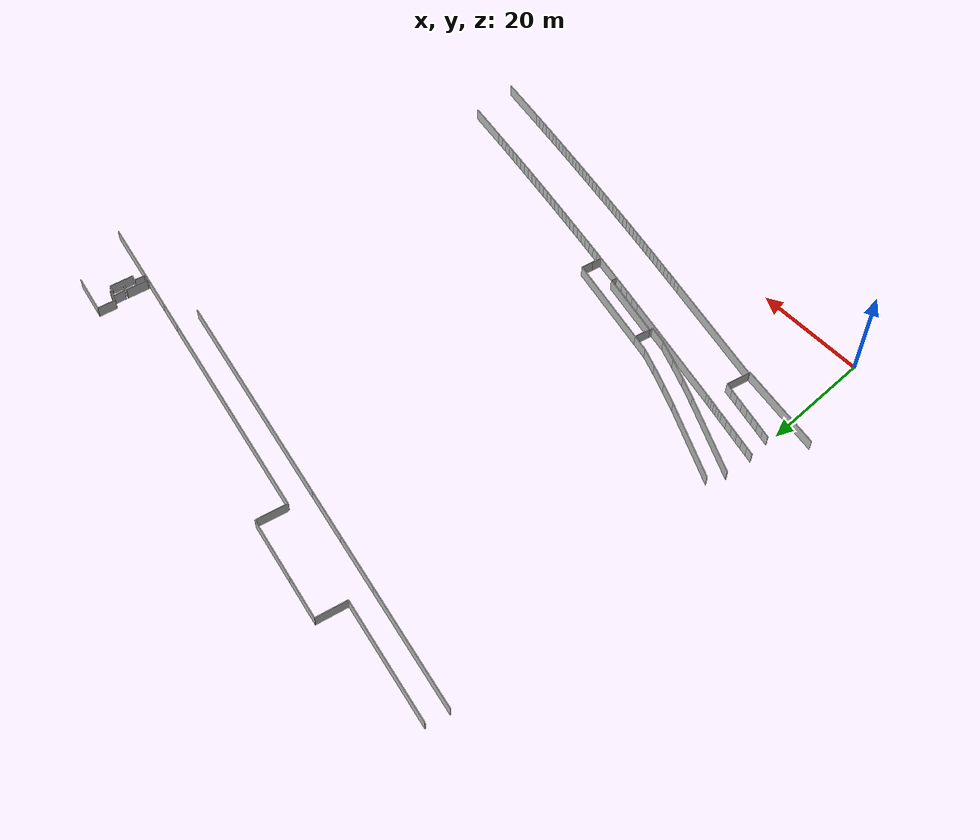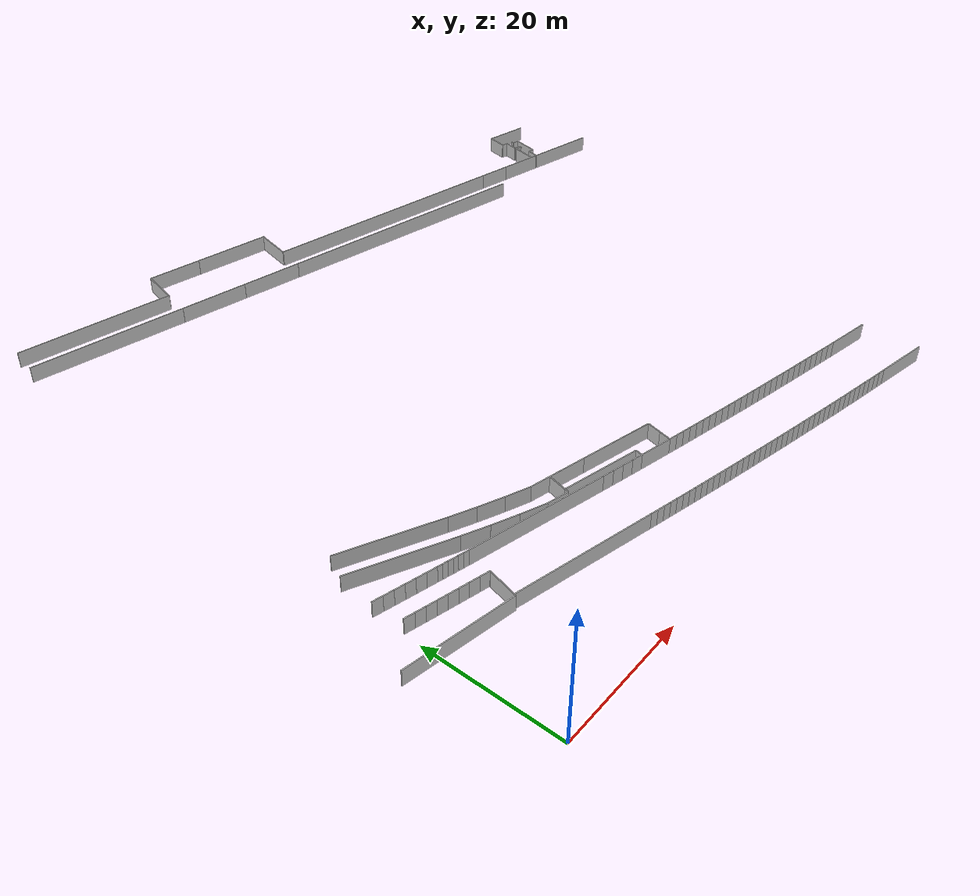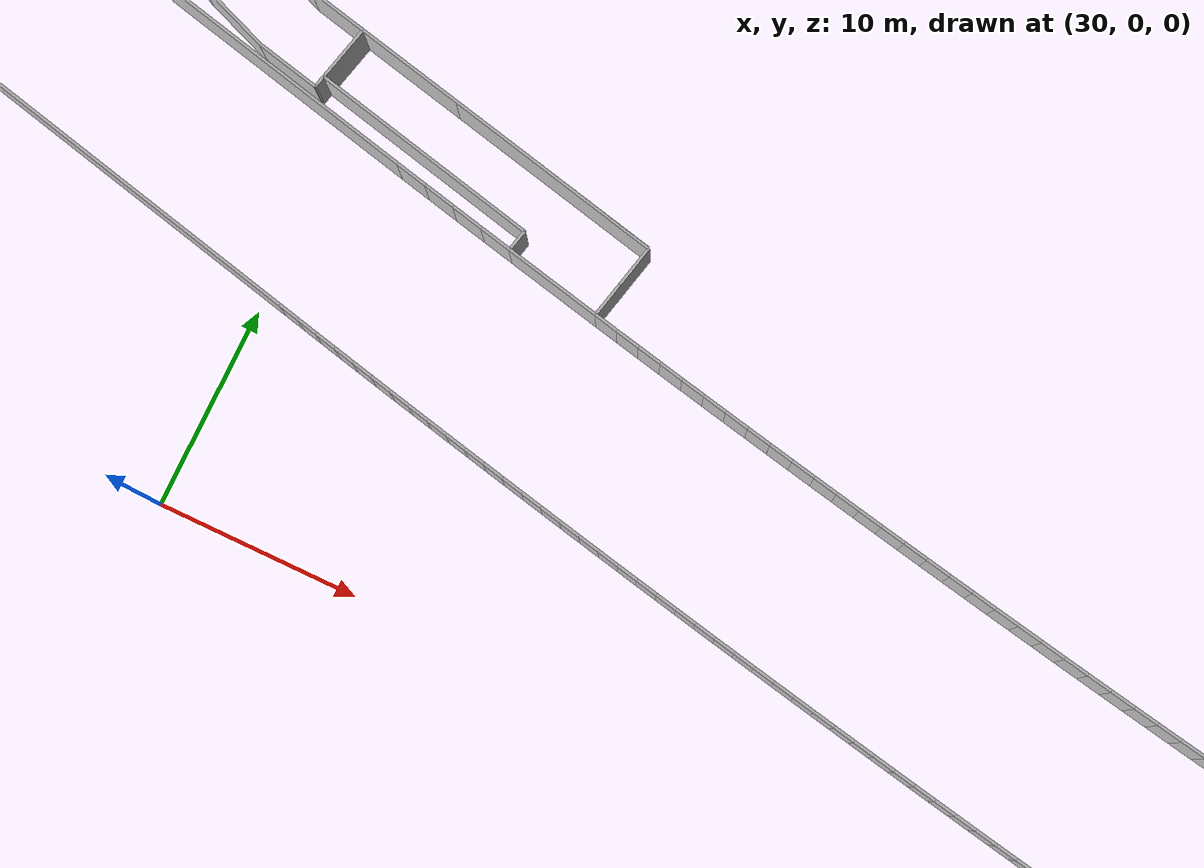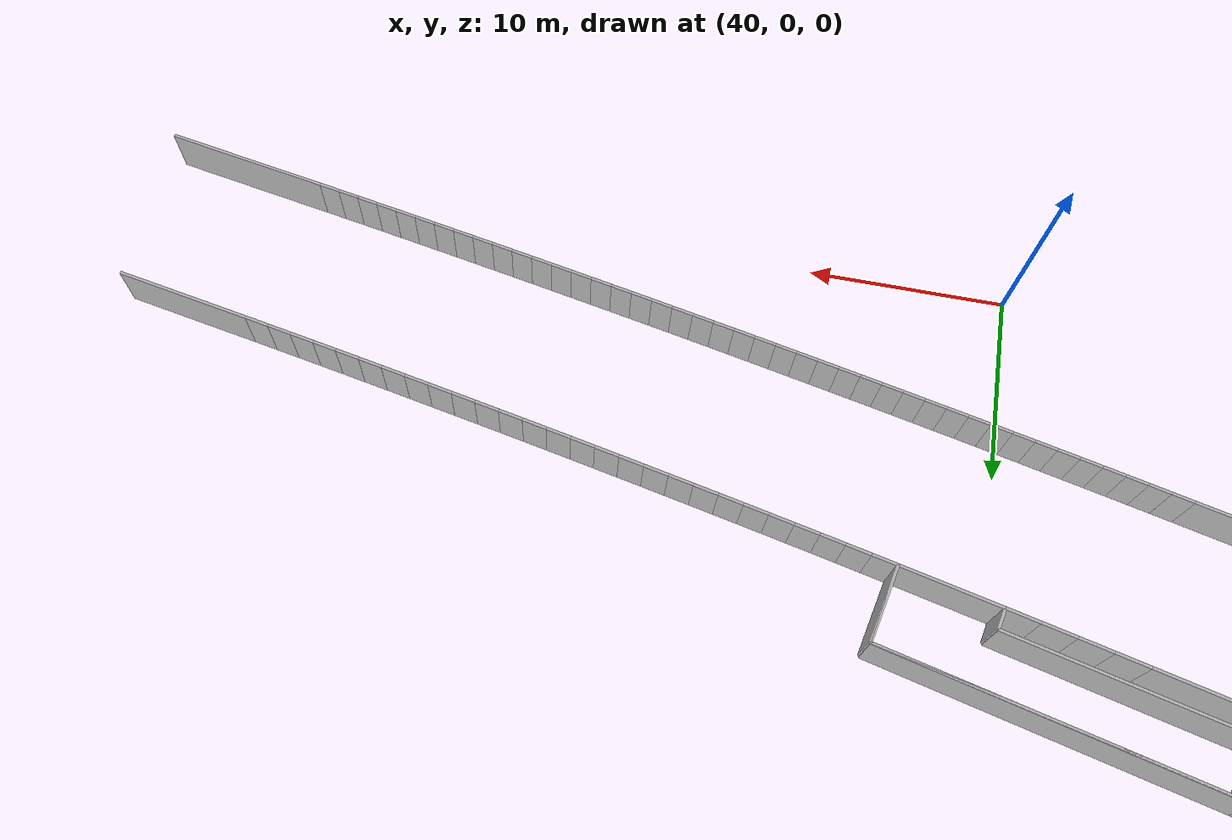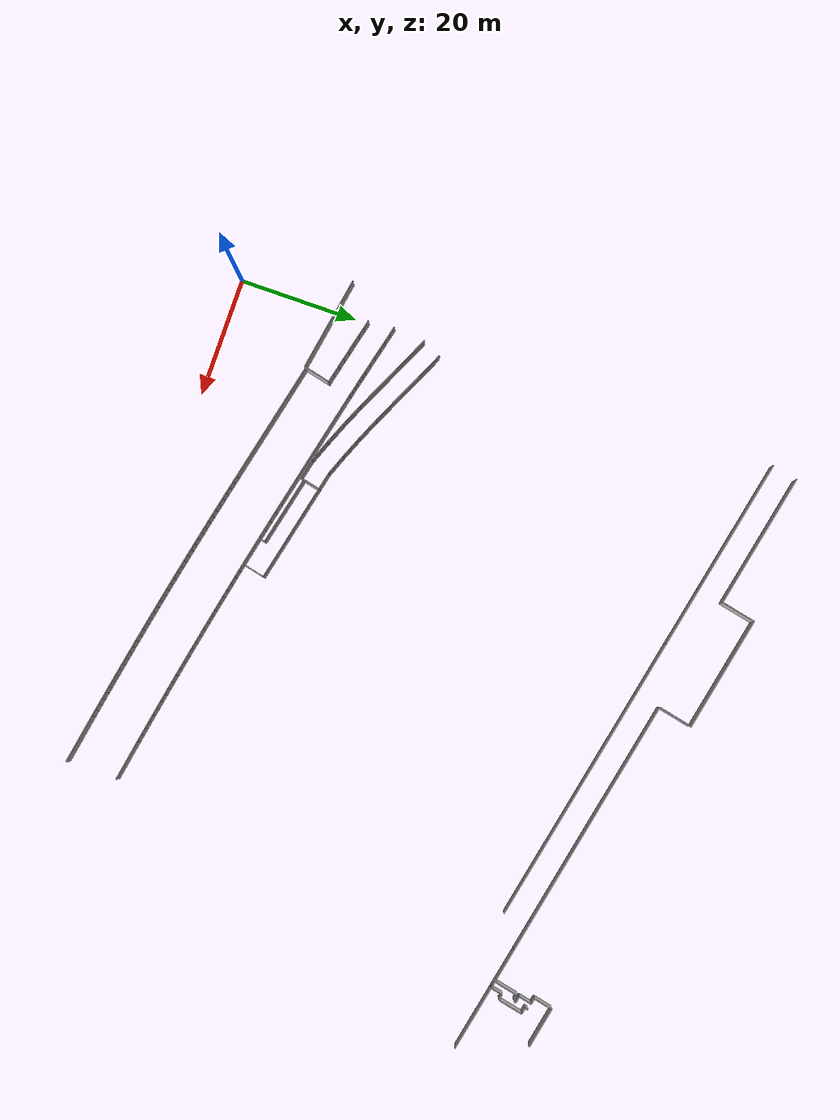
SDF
<?xml version="1.0" ?>
<sdf version="1.6">
  <model name="sps_0902">
    <pose frame="">0 0 0 0 -0 0</pose>
    <static>1</static>
    <self_collide>0</self_collide>
    <allow_auto_disable>0</allow_auto_disable>
    <link name="Wall28">
      <kinematic>0</kinematic>
      <gravity>1</gravity>
      <self_collide>0</self_collide>
      <collision name="collision">
        <geometry>
          <box>
            <size>15.0816 0.15 2.5</size>
          </box>
        </geometry>
        <pose frame="">0 0 0 0 -0 0</pose>
      </collision>
      <visual name="visual">
        <geometry>
          <box>
            <size>15.0816 0.15 2.5</size>
          </box>
        </geometry>
        <pose frame="">0 0 0 0 -0 0</pose>
        <cast_shadows>1</cast_shadows>
        <transparency>0.0</transparency>
      </visual>
      <pose frame="">7.05285 29.0338 1.25 0 -0 2.70048</pose>
    </link>
    <link name="Wall29">
      <kinematic>0</kinematic>
      <gravity>1</gravity>
      <self_collide>0</self_collide>
      <collision name="collision">
        <geometry>
          <box>
            <size>4.01389 0.15 2.5</size>
          </box>
        </geometry>
        <pose frame="">0 0 0 0 -0 0</pose>
      </collision>
      <visual name="visual">
        <geometry>
          <box>
            <size>4.01389 0.15 2.5</size>
          </box>
        </geometry>
        <pose frame="">0 0 0 0 -0 0</pose>
        <cast_shadows>1</cast_shadows>
        <transparency>0.0</transparency>
      </visual>
      <pose frame="">19.4061 23.41 1.25 0 -0 2.74713</pose>
    </link>
    <link name="Wall30">
      <kinematic>0</kinematic>
      <gravity>1</gravity>
      <self_collide>0</self_collide>
      <collision name="collision">
        <geometry>
          <box>
            <size>5.98038 0.15 2.5</size>
          </box>
        </geometry>
        <pose frame="">0 0 0 0 -0 0</pose>
      </collision>
      <visual name="visual">
        <geometry>
          <box>
            <size>5.98038 0.15 2.5</size>
          </box>
        </geometry>
        <pose frame="">0 0 0 0 -0 0</pose>
        <cast_shadows>1</cast_shadows>
        <transparency>0.0</transparency>
      </visual>
      <pose frame="">25.7827 95.2165 1.25 0 0 -1.78506</pose>
    </link>
    <link name="Wall31">
      <kinematic>0</kinematic>
      <gravity>1</gravity>
      <self_collide>0</self_collide>
      <collision name="collision">
        <geometry>
          <box>
            <size>21.1297 0.15 2.5</size>
          </box>
        </geometry>
        <pose frame="">0 0 0 0 -0 0</pose>
      </collision>
      <visual name="visual">
        <geometry>
          <box>
            <size>21.1297 0.15 2.5</size>
          </box>
        </geometry>
        <pose frame="">0 0 0 0 -0 0</pose>
        <cast_shadows>1</cast_shadows>
        <transparency>0.0</transparency>
      </visual>
      <pose frame="">23.0045 21.1647 1.25 0 0 -0.231213</pose>
    </link>
    <link name="Wall118">
      <kinematic>0</kinematic>
      <gravity>1</gravity>
      <self_collide>0</self_collide>
      <collision name="collision">
        <geometry>
          <box>
            <size>16.258 0.15 2.5</size>
          </box>
        </geometry>
        <pose frame="">0 0 0 0 -0 0</pose>
      </collision>
      <visual name="visual">
        <geometry>
          <box>
            <size>16.258 0.15 2.5</size>
          </box>
        </geometry>
        <pose frame="">0 0 0 0 -0 0</pose>
        <cast_shadows>1</cast_shadows>
        <transparency>0.0</transparency>
      </visual>
      <pose frame="">2.6691 16.4683 1.25 0 0 -0.176184</pose>
    </link>
    <link name="Wall119">
      <kinematic>0</kinematic>
      <gravity>1</gravity>
      <self_collide>0</self_collide>
      <collision name="collision">
        <geometry>
          <box>
            <size>5.13421 0.15 2.5</size>
          </box>
        </geometry>
        <pose frame="">0 0 0 0 -0 0</pose>
      </collision>
      <visual name="visual">
        <geometry>
          <box>
            <size>5.13421 0.15 2.5</size>
          </box>
        </geometry>
        <pose frame="">0 0 0 0 -0 0</pose>
        <cast_shadows>1</cast_shadows>
        <transparency>0.0</transparency>
      </visual>
      <pose frame="">86.9778 78.8386 1.25 0 -0 2.92731</pose>
    </link>
    <link name="Wall120">
      <kinematic>0</kinematic>
      <gravity>1</gravity>
      <self_collide>0</self_collide>
      <collision name="collision">
        <geometry>
          <box>
            <size>40.7111 0.15 2.5</size>
          </box>
        </geometry>
        <pose frame="">0 0 0 0 -0 0</pose>
      </collision>
      <visual name="visual">
        <geometry>
          <box>
            <size>40.7111 0.15 2.5</size>
          </box>
        </geometry>
        <pose frame="">0 0 0 0 -0 0</pose>
        <cast_shadows>1</cast_shadows>
        <transparency>0.0</transparency>
      </visual>
      <pose frame="">64.5795 83.7131 1.25 0 -0 2.92731</pose>
    </link>
    <link name="Wall121">
      <kinematic>0</kinematic>
      <gravity>1</gravity>
      <self_collide>0</self_collide>
      <collision name="collision">
        <geometry>
          <box>
            <size>8.60433 0.15 2.5</size>
          </box>
        </geometry>
        <pose frame="">0 0 0 0 -0 0</pose>
      </collision>
      <visual name="visual">
        <geometry>
          <box>
            <size>8.60433 0.15 2.5</size>
          </box>
        </geometry>
        <pose frame="">0 0 0 0 -0 0</pose>
        <cast_shadows>1</cast_shadows>
        <transparency>0.0</transparency>
      </visual>
      <pose frame="">80.2364 0.370085 1.25 0 0 -0.179431</pose>
    </link>
    <link name="Wall123">
      <kinematic>0</kinematic>
      <gravity>1</gravity>
      <self_collide>0</self_collide>
      <collision name="collision">
        <geometry>
          <box>
            <size>7.06281 0.15 2.5</size>
          </box>
        </geometry>
        <pose frame="">0 0 0 0 -0 0</pose>
      </collision>
      <visual name="visual">
        <geometry>
          <box>
            <size>7.06281 0.15 2.5</size>
          </box>
        </geometry>
        <pose frame="">0 0 0 0 -0 0</pose>
        <cast_shadows>1</cast_shadows>
        <transparency>0.0</transparency>
      </visual>
      <pose frame="">80.9947 8.87143 1.25 0 0 -0.179443</pose>
    </link>
    <link name="Wall196">
      <kinematic>0</kinematic>
      <gravity>1</gravity>
      <self_collide>0</self_collide>
      <collision name="collision">
        <geometry>
          <box>
            <size>3.94369 0.15 2.5</size>
          </box>
        </geometry>
        <pose frame="">0 0 0 0 -0 0</pose>
      </collision>
      <visual name="visual">
        <geometry>
          <box>
            <size>3.94369 0.15 2.5</size>
          </box>
        </geometry>
        <pose frame="">0 0 0 0 -0 0</pose>
        <cast_shadows>1</cast_shadows>
        <transparency>0.0</transparency>
      </visual>
      <pose frame="">17.1317 28.1964 1.25 0 0 -0.417479</pose>
    </link>
    <link name="Wall197">
      <kinematic>0</kinematic>
      <gravity>1</gravity>
      <self_collide>0</self_collide>
      <collision name="collision">
        <geometry>
          <box>
            <size>21.1844 0.15 2.5</size>
          </box>
        </geometry>
        <pose frame="">0 0 0 0 -0 0</pose>
      </collision>
      <visual name="visual">
        <geometry>
          <box>
            <size>21.1844 0.15 2.5</size>
          </box>
        </geometry>
        <pose frame="">0 0 0 0 -0 0</pose>
        <cast_shadows>1</cast_shadows>
        <transparency>0.0</transparency>
      </visual>
      <pose frame="">21.0443 12.8755 1.25 0 0 -0.229613</pose>
    </link>
    <link name="Wall198">
      <kinematic>0</kinematic>
      <gravity>1</gravity>
      <self_collide>0</self_collide>
      <collision name="collision">
        <geometry>
          <box>
            <size>5.98036 0.15 2.5</size>
          </box>
        </geometry>
        <pose frame="">0 0 0 0 -0 0</pose>
      </collision>
      <visual name="visual">
        <geometry>
          <box>
            <size>5.98036 0.15 2.5</size>
          </box>
        </geometry>
        <pose frame="">0 0 0 0 -0 0</pose>
        <cast_shadows>1</cast_shadows>
        <transparency>0.0</transparency>
      </visual>
      <pose frame="">45.3254 90.9635 1.25 0 0 -1.78509</pose>
    </link>
    <link name="Wall287">
      <kinematic>0</kinematic>
      <gravity>1</gravity>
      <self_collide>0</self_collide>
      <collision name="collision">
        <geometry>
          <box>
            <size>3.93435 0.15 2.5</size>
          </box>
        </geometry>
        <pose frame="">0 0 0 0 -0 0</pose>
      </collision>
      <visual name="visual">
        <geometry>
          <box>
            <size>3.93435 0.15 2.5</size>
          </box>
        </geometry>
        <pose frame="">0 0 0 0 -0 0</pose>
        <cast_shadows>1</cast_shadows>
        <transparency>0.0</transparency>
      </visual>
      <pose frame="">20.7505 26.6414 1.25 0 0 -0.394179</pose>
    </link>
    <link name="Wall288">
      <kinematic>0</kinematic>
      <gravity>1</gravity>
      <self_collide>0</self_collide>
      <collision name="collision">
        <geometry>
          <box>
            <size>9.50174 0.15 2.5</size>
          </box>
        </geometry>
        <pose frame="">0 0 0 0 -0 0</pose>
      </collision>
      <visual name="visual">
        <geometry>
          <box>
            <size>9.50174 0.15 2.5</size>
          </box>
        </geometry>
        <pose frame="">0 0 0 0 -0 0</pose>
        <cast_shadows>1</cast_shadows>
        <transparency>0.0</transparency>
      </visual>
      <pose frame="">39.1117 84.7528 1.25 0 -0 2.92731</pose>
    </link>
    <link name="Wall289">
      <kinematic>0</kinematic>
      <gravity>1</gravity>
      <self_collide>0</self_collide>
      <collision name="collision">
        <geometry>
          <box>
            <size>10.4985 0.15 2.5</size>
          </box>
        </geometry>
        <pose frame="">0 0 0 0 -0 0</pose>
      </collision>
      <visual name="visual">
        <geometry>
          <box>
            <size>10.4985 0.15 2.5</size>
          </box>
        </geometry>
        <pose frame="">0 0 0 0 -0 0</pose>
        <cast_shadows>1</cast_shadows>
        <transparency>0.0</transparency>
      </visual>
      <pose frame="">29.3403 86.8793 1.25 0 -0 2.92731</pose>
    </link>
    <link name="Wall290">
      <kinematic>0</kinematic>
      <gravity>1</gravity>
      <self_collide>0</self_collide>
      <collision name="collision">
        <geometry>
          <box>
            <size>5.6374 0.15 2.5</size>
          </box>
        </geometry>
        <pose frame="">0 0 0 0 -0 0</pose>
      </collision>
      <visual name="visual">
        <geometry>
          <box>
            <size>5.6374 0.15 2.5</size>
          </box>
        </geometry>
        <pose frame="">0 0 0 0 -0 0</pose>
        <cast_shadows>1</cast_shadows>
        <transparency>0.0</transparency>
      </visual>
      <pose frame="">31.7244 23.2149 1.25 0 0 -0.229042</pose>
    </link>
    <link name="Wall291">
      <kinematic>0</kinematic>
      <gravity>1</gravity>
      <self_collide>0</self_collide>
      <collision name="collision">
        <geometry>
          <box>
            <size>11.3628 0.15 2.5</size>
          </box>
        </geometry>
        <pose frame="">0 0 0 0 -0 0</pose>
      </collision>
      <visual name="visual">
        <geometry>
          <box>
            <size>11.3628 0.15 2.5</size>
          </box>
        </geometry>
        <pose frame="">0 0 0 0 -0 0</pose>
        <cast_shadows>1</cast_shadows>
        <transparency>0.0</transparency>
      </visual>
      <pose frame="">40.0025 21.285 1.25 0 0 -0.229042</pose>
    </link>
    <link name="Wall354">
      <kinematic>0</kinematic>
      <gravity>1</gravity>
      <self_collide>0</self_collide>
      <collision name="collision">
        <geometry>
          <box>
            <size>4.02733 0.15 2.5</size>
          </box>
        </geometry>
        <pose frame="">0 0 0 0 -0 0</pose>
      </collision>
      <visual name="visual">
        <geometry>
          <box>
            <size>4.02733 0.15 2.5</size>
          </box>
        </geometry>
        <pose frame="">0 0 0 0 -0 0</pose>
        <cast_shadows>1</cast_shadows>
        <transparency>0.0</transparency>
      </visual>
      <pose frame="">15.7125 24.9978 1.25 0 -0 2.72409</pose>
    </link>
    <link name="Wall355">
      <kinematic>0</kinematic>
      <gravity>1</gravity>
      <self_collide>0</self_collide>
      <collision name="collision">
        <geometry>
          <box>
            <size>3.95796 0.15 2.5</size>
          </box>
        </geometry>
        <pose frame="">0 0 0 0 -0 0</pose>
      </collision>
      <visual name="visual">
        <geometry>
          <box>
            <size>3.95796 0.15 2.5</size>
          </box>
        </geometry>
        <pose frame="">0 0 0 0 -0 0</pose>
        <cast_shadows>1</cast_shadows>
        <transparency>0.0</transparency>
      </visual>
      <pose frame="">23.1028 21.9201 1.25 0 -0 2.76998</pose>
    </link>
    <link name="Wall356">
      <kinematic>0</kinematic>
      <gravity>1</gravity>
      <self_collide>0</self_collide>
      <collision name="collision">
        <geometry>
          <box>
            <size>23.6493 0.15 2.5</size>
          </box>
        </geometry>
        <pose frame="">0 0 0 0 -0 0</pose>
      </collision>
      <visual name="visual">
        <geometry>
          <box>
            <size>23.6493 0.15 2.5</size>
          </box>
        </geometry>
        <pose frame="">0 0 0 0 -0 0</pose>
        <cast_shadows>1</cast_shadows>
        <transparency>0.0</transparency>
      </visual>
      <pose frame="">13.5927 94.8092 1.25 0 -0 2.92731</pose>
    </link>
    <link name="Wall357">
      <kinematic>0</kinematic>
      <gravity>1</gravity>
      <self_collide>0</self_collide>
      <collision name="collision">
        <geometry>
          <box>
            <size>3.07591 0.15 2.5</size>
          </box>
        </geometry>
        <pose frame="">0 0 0 0 -0 0</pose>
      </collision>
      <visual name="visual">
        <geometry>
          <box>
            <size>3.07591 0.15 2.5</size>
          </box>
        </geometry>
        <pose frame="">0 0 0 0 -0 0</pose>
        <cast_shadows>1</cast_shadows>
        <transparency>0.0</transparency>
      </visual>
      <pose frame="">27.4815 24.204 1.25 0 0 -0.229</pose>
    </link>
    <link name="Wall364">
      <kinematic>0</kinematic>
      <gravity>1</gravity>
      <self_collide>0</self_collide>
      <collision name="collision">
        <geometry>
          <box>
            <size>41.6686 0.15 2.5</size>
          </box>
        </geometry>
        <pose frame="">0 0 0 0 -0 0</pose>
      </collision>
      <visual name="visual">
        <geometry>
          <box>
            <size>41.6686 0.15 2.5</size>
          </box>
        </geometry>
        <pose frame="">0 0 0 0 -0 0</pose>
        <cast_shadows>1</cast_shadows>
        <transparency>0.0</transparency>
      </visual>
      <pose frame="">64.1117 79.312 1.25 0 -0 2.9273</pose>
    </link>
    <link name="Wall435">
      <kinematic>0</kinematic>
      <gravity>1</gravity>
      <self_collide>0</self_collide>
      <collision name="collision">
        <geometry>
          <box>
            <size>0.179735 0.15 2.5</size>
          </box>
        </geometry>
        <pose frame="">0 0 0 0 -0 0</pose>
      </collision>
      <visual name="visual">
        <geometry>
          <box>
            <size>0.179735 0.15 2.5</size>
          </box>
        </geometry>
        <pose frame="">0 0 0 0 -0 0</pose>
        <cast_shadows>1</cast_shadows>
        <transparency>0.0</transparency>
      </visual>
      <pose frame="">11.743 19.5065 1.25 0 -0 1.33603</pose>
    </link>
    <link name="Wall436">
      <kinematic>0</kinematic>
      <gravity>1</gravity>
      <self_collide>0</self_collide>
      <collision name="collision">
        <geometry>
          <box>
            <size>23.6497 0.15 2.5</size>
          </box>
        </geometry>
        <pose frame="">0 0 0 0 -0 0</pose>
      </collision>
      <visual name="visual">
        <geometry>
          <box>
            <size>23.6497 0.15 2.5</size>
          </box>
        </geometry>
        <pose frame="">0 0 0 0 -0 0</pose>
        <cast_shadows>1</cast_shadows>
        <transparency>0.0</transparency>
      </visual>
      <pose frame="">12.6567 90.5101 1.25 0 -0 2.9273</pose>
    </link>
    <link name="Wall437">
      <kinematic>0</kinematic>
      <gravity>1</gravity>
      <self_collide>0</self_collide>
      <collision name="collision">
        <geometry>
          <box>
            <size>11.7608 0.15 2.5</size>
          </box>
        </geometry>
        <pose frame="">0 0 0 0 -0 0</pose>
      </collision>
      <visual name="visual">
        <geometry>
          <box>
            <size>11.7608 0.15 2.5</size>
          </box>
        </geometry>
        <pose frame="">0 0 0 0 -0 0</pose>
        <cast_shadows>1</cast_shadows>
        <transparency>0.0</transparency>
      </visual>
      <pose frame="">40.2154 95.1357 1.25 0 -0 2.92731</pose>
    </link>
    <link name="Wall438">
      <kinematic>0</kinematic>
      <gravity>1</gravity>
      <self_collide>0</self_collide>
      <collision name="collision">
        <geometry>
          <box>
            <size>8.23941 0.15 2.5</size>
          </box>
        </geometry>
        <pose frame="">0 0 0 0 -0 0</pose>
      </collision>
      <visual name="visual">
        <geometry>
          <box>
            <size>8.23941 0.15 2.5</size>
          </box>
        </geometry>
        <pose frame="">0 0 0 0 -0 0</pose>
        <cast_shadows>1</cast_shadows>
        <transparency>0.0</transparency>
      </visual>
      <pose frame="">30.444 97.2623 1.25 0 -0 2.92731</pose>
    </link>
    <link name="Wall532">
      <kinematic>0</kinematic>
      <gravity>1</gravity>
      <self_collide>0</self_collide>
      <collision name="collision">
        <geometry>
          <box>
            <size>0.249583 0.15 2.5</size>
          </box>
        </geometry>
        <pose frame="">0 0 0 0 -0 0</pose>
      </collision>
      <visual name="visual">
        <geometry>
          <box>
            <size>0.249583 0.15 2.5</size>
          </box>
        </geometry>
        <pose frame="">0 0 0 0 -0 0</pose>
        <cast_shadows>1</cast_shadows>
        <transparency>0.0</transparency>
      </visual>
      <pose frame="">10.7012 15.1649 1.25 0 -0 1.33709</pose>
    </link>
    <link name="Wall533">
      <kinematic>0</kinematic>
      <gravity>1</gravity>
      <self_collide>0</self_collide>
      <collision name="collision">
        <geometry>
          <box>
            <size>14.9395 0.15 2.5</size>
          </box>
        </geometry>
        <pose frame="">0 0 0 0 -0 0</pose>
      </collision>
      <visual name="visual">
        <geometry>
          <box>
            <size>14.9395 0.15 2.5</size>
          </box>
        </geometry>
        <pose frame="">0 0 0 0 -0 0</pose>
        <cast_shadows>1</cast_shadows>
        <transparency>0.0</transparency>
      </visual>
      <pose frame="">8.57455 32.1851 1.25 0 0 -0.441118</pose>
    </link>
    <link name="Wall534">
      <kinematic>0</kinematic>
      <gravity>1</gravity>
      <self_collide>0</self_collide>
      <collision name="collision">
        <geometry>
          <box>
            <size>3.66754 0.15 2.5</size>
          </box>
        </geometry>
        <pose frame="">0 0 0 0 -0 0</pose>
      </collision>
      <visual name="visual">
        <geometry>
          <box>
            <size>3.66754 0.15 2.5</size>
          </box>
        </geometry>
        <pose frame="">0 0 0 0 -0 0</pose>
        <cast_shadows>1</cast_shadows>
        <transparency>0.0</transparency>
      </visual>
      <pose frame="">24.2753 25.2195 1.25 0 0 -0.371909</pose>
    </link>
    <link name="Wall535">
      <kinematic>0</kinematic>
      <gravity>1</gravity>
      <self_collide>0</self_collide>
      <collision name="collision">
        <geometry>
          <box>
            <size>3.32587 0.15 2.5</size>
          </box>
        </geometry>
        <pose frame="">0 0 0 0 -0 0</pose>
      </collision>
      <visual name="visual">
        <geometry>
          <box>
            <size>3.32587 0.15 2.5</size>
          </box>
        </geometry>
        <pose frame="">0 0 0 0 -0 0</pose>
        <cast_shadows>1</cast_shadows>
        <transparency>0.0</transparency>
      </visual>
      <pose frame="">26.5662 20.8238 1.25 0 -0 2.91247</pose>
    </link>
    <link name="Wall536">
      <kinematic>0</kinematic>
      <gravity>1</gravity>
      <self_collide>0</self_collide>
      <collision name="collision">
        <geometry>
          <box>
            <size>0.61782 0.15 2.5</size>
          </box>
        </geometry>
        <pose frame="">0 0 0 0 -0 0</pose>
      </collision>
      <visual name="visual">
        <geometry>
          <box>
            <size>0.61782 0.15 2.5</size>
          </box>
        </geometry>
        <pose frame="">0 0 0 0 -0 0</pose>
        <cast_shadows>1</cast_shadows>
        <transparency>0.0</transparency>
      </visual>
      <pose frame="">28.2556 20.747 1.25 0 0 -1.79941</pose>
    </link>
    <link name="Wall537">
      <kinematic>0</kinematic>
      <gravity>1</gravity>
      <self_collide>0</self_collide>
      <collision name="collision">
        <geometry>
          <box>
            <size>2.15842 0.15 2.5</size>
          </box>
        </geometry>
        <pose frame="">0 0 0 0 -0 0</pose>
      </collision>
      <visual name="visual">
        <geometry>
          <box>
            <size>2.15842 0.15 2.5</size>
          </box>
        </geometry>
        <pose frame="">0 0 0 0 -0 0</pose>
        <cast_shadows>1</cast_shadows>
        <transparency>0.0</transparency>
      </visual>
      <pose frame="">45.2903 18.9441 1.25 0 0 -1.79996</pose>
    </link>
    <link name="Wall538">
      <kinematic>0</kinematic>
      <gravity>1</gravity>
      <self_collide>0</self_collide>
      <collision name="collision">
        <geometry>
          <box>
            <size>1.77993 0.15 2.5</size>
          </box>
        </geometry>
        <pose frame="">0 0 0 0 -0 0</pose>
      </collision>
      <visual name="visual">
        <geometry>
          <box>
            <size>1.77993 0.15 2.5</size>
          </box>
        </geometry>
        <pose frame="">0 0 0 0 -0 0</pose>
        <cast_shadows>1</cast_shadows>
        <transparency>0.0</transparency>
      </visual>
      <pose frame="">44.843 17.0264 1.25 0 0 -1.79996</pose>
    </link>
    <link name="Wall539">
      <kinematic>0</kinematic>
      <gravity>1</gravity>
      <self_collide>0</self_collide>
      <collision name="collision">
        <geometry>
          <box>
            <size>18.5 0.15 2.5</size>
          </box>
        </geometry>
        <pose frame="">0 0 0 0 -0 0</pose>
      </collision>
      <visual name="visual">
        <geometry>
          <box>
            <size>18.5 0.15 2.5</size>
          </box>
        </geometry>
        <pose frame="">0 0 0 0 -0 0</pose>
        <cast_shadows>1</cast_shadows>
        <transparency>0.0</transparency>
      </visual>
      <pose frame="">98.5246 76.3257 1.25 0 0 -0.214283</pose>
    </link>
    <link name="Wall995">
      <kinematic>0</kinematic>
      <gravity>1</gravity>
      <self_collide>0</self_collide>
      <collision name="collision">
        <geometry>
          <box>
            <size>0.249583 0.15 2.5</size>
          </box>
        </geometry>
        <pose frame="">0 0 0 0 -0 0</pose>
      </collision>
      <visual name="visual">
        <geometry>
          <box>
            <size>0.249583 0.15 2.5</size>
          </box>
        </geometry>
        <pose frame="">0 0 0 0 -0 0</pose>
        <cast_shadows>1</cast_shadows>
        <transparency>0.0</transparency>
      </visual>
      <pose frame="">10.7012 15.1649 1.25 0 0 -1.80451</pose>
    </link>
    <link name="Wall1007">
      <kinematic>0</kinematic>
      <gravity>1</gravity>
      <self_collide>0</self_collide>
      <collision name="collision">
        <geometry>
          <box>
            <size>4.2502 0.15 2.5</size>
          </box>
        </geometry>
        <pose frame="">0 0 0 0 -0 0</pose>
      </collision>
      <visual name="visual">
        <geometry>
          <box>
            <size>4.2502 0.15 2.5</size>
          </box>
        </geometry>
        <pose frame="">0 0 0 0 -0 0</pose>
        <cast_shadows>1</cast_shadows>
        <transparency>0.0</transparency>
      </visual>
      <pose frame="">11.2261 17.3527 1.25 0 0 -1.80637</pose>
    </link>
    <link name="Wall1008">
      <kinematic>0</kinematic>
      <gravity>1</gravity>
      <self_collide>0</self_collide>
      <collision name="collision">
        <geometry>
          <box>
            <size>2.8821 0.15 2.5</size>
          </box>
        </geometry>
        <pose frame="">0 0 0 0 -0 0</pose>
      </collision>
      <visual name="visual">
        <geometry>
          <box>
            <size>2.8821 0.15 2.5</size>
          </box>
        </geometry>
        <pose frame="">0 0 0 0 -0 0</pose>
        <cast_shadows>1</cast_shadows>
        <transparency>0.0</transparency>
      </visual>
      <pose frame="">28.6525 22.4514 1.25 0 -0 1.34202</pose>
    </link>
    <link name="Wall1009">
      <kinematic>0</kinematic>
      <gravity>1</gravity>
      <self_collide>0</self_collide>
      <collision name="collision">
        <geometry>
          <box>
            <size>17.0002 0.15 2.5</size>
          </box>
        </geometry>
        <pose frame="">0 0 0 0 -0 0</pose>
      </collision>
      <visual name="visual">
        <geometry>
          <box>
            <size>17.0002 0.15 2.5</size>
          </box>
        </geometry>
        <pose frame="">0 0 0 0 -0 0</pose>
        <cast_shadows>1</cast_shadows>
        <transparency>0.0</transparency>
      </visual>
      <pose frame="">37.2574 21.925 1.25 0 0 -0.229042</pose>
    </link>
    <link name="Wall1010">
      <kinematic>0</kinematic>
      <gravity>1</gravity>
      <self_collide>0</self_collide>
      <collision name="collision">
        <geometry>
          <box>
            <size>3.93835 0.15 2.5</size>
          </box>
        </geometry>
        <pose frame="">0 0 0 0 -0 0</pose>
      </collision>
      <visual name="visual">
        <geometry>
          <box>
            <size>3.93835 0.15 2.5</size>
          </box>
        </geometry>
        <pose frame="">0 0 0 0 -0 0</pose>
        <cast_shadows>1</cast_shadows>
        <transparency>0.0</transparency>
      </visual>
      <pose frame="">45.0882 18.0774 1.25 0 0 -1.79996</pose>
    </link>
    <link name="Wall1011">
      <kinematic>0</kinematic>
      <gravity>1</gravity>
      <self_collide>0</self_collide>
      <collision name="collision">
        <geometry>
          <box>
            <size>4.99972 0.15 2.5</size>
          </box>
        </geometry>
        <pose frame="">0 0 0 0 -0 0</pose>
      </collision>
      <visual name="visual">
        <geometry>
          <box>
            <size>4.99972 0.15 2.5</size>
          </box>
        </geometry>
        <pose frame="">0 0 0 0 -0 0</pose>
        <cast_shadows>1</cast_shadows>
        <transparency>0.0</transparency>
      </visual>
      <pose frame="">42.2015 16.7066 1.25 0 -0 2.92103</pose>
    </link>
    <link name="Wall1012">
      <kinematic>0</kinematic>
      <gravity>1</gravity>
      <self_collide>0</self_collide>
      <collision name="collision">
        <geometry>
          <box>
            <size>1.08065 0.15 2.5</size>
          </box>
        </geometry>
        <pose frame="">0 0 0 0 -0 0</pose>
      </collision>
      <visual name="visual">
        <geometry>
          <box>
            <size>1.08065 0.15 2.5</size>
          </box>
        </geometry>
        <pose frame="">0 0 0 0 -0 0</pose>
        <cast_shadows>1</cast_shadows>
        <transparency>0.0</transparency>
      </visual>
      <pose frame="">39.8854 17.7796 1.25 0 -0 1.34076</pose>
    </link>
    <link name="Wall1013">
      <kinematic>0</kinematic>
      <gravity>1</gravity>
      <self_collide>0</self_collide>
      <collision name="collision">
        <geometry>
          <box>
            <size>12.0005 0.15 2.5</size>
          </box>
        </geometry>
        <pose frame="">0 0 0 0 -0 0</pose>
      </collision>
      <visual name="visual">
        <geometry>
          <box>
            <size>12.0005 0.15 2.5</size>
          </box>
        </geometry>
        <pose frame="">0 0 0 0 -0 0</pose>
        <cast_shadows>1</cast_shadows>
        <transparency>0.0</transparency>
      </visual>
      <pose frame="">34.1671 19.6768 1.25 0 -0 2.91105</pose>
    </link>
    <link name="Wall2366">
      <kinematic>0</kinematic>
      <gravity>1</gravity>
      <self_collide>0</self_collide>
      <collision name="collision">
        <geometry>
          <box>
            <size>0.499995 0.15 2.5</size>
          </box>
        </geometry>
        <pose frame="">0 0 0 0 -0 0</pose>
      </collision>
      <visual name="visual">
        <geometry>
          <box>
            <size>0.499995 0.15 2.5</size>
          </box>
        </geometry>
        <pose frame="">0 0 0 0 -0 0</pose>
        <cast_shadows>1</cast_shadows>
        <transparency>0.0</transparency>
      </visual>
      <pose frame="">97.8079 83.2656 1.25 0 0 -1.78483</pose>
    </link>
    <link name="Wall2367">
      <kinematic>0</kinematic>
      <gravity>1</gravity>
      <self_collide>0</self_collide>
      <collision name="collision">
        <geometry>
          <box>
            <size>1.07993 0.15 2.5</size>
          </box>
        </geometry>
        <pose frame="">0 0 0 0 -0 0</pose>
      </collision>
      <visual name="visual">
        <geometry>
          <box>
            <size>1.07993 0.15 2.5</size>
          </box>
        </geometry>
        <pose frame="">0 0 0 0 -0 0</pose>
        <cast_shadows>1</cast_shadows>
        <transparency>0.0</transparency>
      </visual>
      <pose frame="">98.2825 82.9065 1.25 0 0 -0.214255</pose>
    </link>
    <link name="Wall2368">
      <kinematic>0</kinematic>
      <gravity>1</gravity>
      <self_collide>0</self_collide>
      <collision name="collision">
        <geometry>
          <box>
            <size>4.30218 0.15 2.5</size>
          </box>
        </geometry>
        <pose frame="">0 0 0 0 -0 0</pose>
      </collision>
      <visual name="visual">
        <geometry>
          <box>
            <size>4.30218 0.15 2.5</size>
          </box>
        </geometry>
        <pose frame="">0 0 0 0 -0 0</pose>
        <cast_shadows>1</cast_shadows>
        <transparency>0.0</transparency>
      </visual>
      <pose frame="">98.3527 80.6898 1.25 0 0 -1.78507</pose>
    </link>
    <link name="Wall2369">
      <kinematic>0</kinematic>
      <gravity>1</gravity>
      <self_collide>0</self_collide>
      <collision name="collision">
        <geometry>
          <box>
            <size>0.99991 0.15 2.5</size>
          </box>
        </geometry>
        <pose frame="">0 0 0 0 -0 0</pose>
      </collision>
      <visual name="visual">
        <geometry>
          <box>
            <size>0.99991 0.15 2.5</size>
          </box>
        </geometry>
        <pose frame="">0 0 0 0 -0 0</pose>
        <cast_shadows>1</cast_shadows>
        <transparency>0.0</transparency>
      </visual>
      <pose frame="">97.4068 78.6942 1.25 0 -0 2.92735</pose>
    </link>
    <link name="Wall2370">
      <kinematic>0</kinematic>
      <gravity>1</gravity>
      <self_collide>0</self_collide>
      <collision name="collision">
        <geometry>
          <box>
            <size>1.72873 0.15 2.5</size>
          </box>
        </geometry>
        <pose frame="">0 0 0 0 -0 0</pose>
      </collision>
      <visual name="visual">
        <geometry>
          <box>
            <size>1.72873 0.15 2.5</size>
          </box>
        </geometry>
        <pose frame="">0 0 0 0 -0 0</pose>
        <cast_shadows>1</cast_shadows>
        <transparency>0.0</transparency>
      </visual>
      <pose frame="">96.7345 77.9559 1.25 0 0 -1.78505</pose>
    </link>
    <link name="Wall2371">
      <kinematic>0</kinematic>
      <gravity>1</gravity>
      <self_collide>0</self_collide>
      <collision name="collision">
        <geometry>
          <box>
            <size>0.347934 0.15 2.5</size>
          </box>
        </geometry>
        <pose frame="">0 0 0 0 -0 0</pose>
      </collision>
      <visual name="visual">
        <geometry>
          <box>
            <size>0.347934 0.15 2.5</size>
          </box>
        </geometry>
        <pose frame="">0 0 0 0 -0 0</pose>
        <cast_shadows>1</cast_shadows>
        <transparency>0.0</transparency>
      </visual>
      <pose frame="">96.5137 76.9413 1.25 0 0 -1.78522</pose>
    </link>
    <link name="Wall2372">
      <kinematic>0</kinematic>
      <gravity>1</gravity>
      <self_collide>0</self_collide>
      <collision name="collision">
        <geometry>
          <box>
            <size>1.15995 0.15 2.5</size>
          </box>
        </geometry>
        <pose frame="">0 0 0 0 -0 0</pose>
      </collision>
      <visual name="visual">
        <geometry>
          <box>
            <size>1.15995 0.15 2.5</size>
          </box>
        </geometry>
        <pose frame="">0 0 0 0 -0 0</pose>
        <cast_shadows>1</cast_shadows>
        <transparency>0.0</transparency>
      </visual>
      <pose frame="">95.91 76.8948 1.25 0 -0 2.92706</pose>
    </link>
    <link name="Wall2373">
      <kinematic>0</kinematic>
      <gravity>1</gravity>
      <self_collide>0</self_collide>
      <collision name="collision">
        <geometry>
          <box>
            <size>0.347981 0.15 2.5</size>
          </box>
        </geometry>
        <pose frame="">0 0 0 0 -0 0</pose>
      </collision>
      <visual name="visual">
        <geometry>
          <box>
            <size>0.347981 0.15 2.5</size>
          </box>
        </geometry>
        <pose frame="">0 0 0 0 -0 0</pose>
        <cast_shadows>1</cast_shadows>
        <transparency>0.0</transparency>
      </visual>
      <pose frame="">95.3803 77.1883 1.25 0 -0 1.35658</pose>
    </link>
    <link name="Wall2374">
      <kinematic>0</kinematic>
      <gravity>1</gravity>
      <self_collide>0</self_collide>
      <collision name="collision">
        <geometry>
          <box>
            <size>3.87829 0.15 2.5</size>
          </box>
        </geometry>
        <pose frame="">0 0 0 0 -0 0</pose>
      </collision>
      <visual name="visual">
        <geometry>
          <box>
            <size>3.87829 0.15 2.5</size>
          </box>
        </geometry>
        <pose frame="">0 0 0 0 -0 0</pose>
        <cast_shadows>1</cast_shadows>
        <transparency>0.0</transparency>
      </visual>
      <pose frame="">95.8296 79.2531 1.25 0 -0 1.35655</pose>
    </link>
    <link name="Wall2375">
      <kinematic>0</kinematic>
      <gravity>1</gravity>
      <self_collide>0</self_collide>
      <collision name="collision">
        <geometry>
          <box>
            <size>1.07989 0.15 2.5</size>
          </box>
        </geometry>
        <pose frame="">0 0 0 0 -0 0</pose>
      </collision>
      <visual name="visual">
        <geometry>
          <box>
            <size>1.07989 0.15 2.5</size>
          </box>
        </geometry>
        <pose frame="">0 0 0 0 -0 0</pose>
        <cast_shadows>1</cast_shadows>
        <transparency>0.0</transparency>
      </visual>
      <pose frame="">96.7695 81.0332 1.25 0 0 -0.214089</pose>
    </link>
    <link name="Wall2376">
      <kinematic>0</kinematic>
      <gravity>1</gravity>
      <self_collide>0</self_collide>
      <collision name="collision">
        <geometry>
          <box>
            <size>0.399937 0.15 2.5</size>
          </box>
        </geometry>
        <pose frame="">0 0 0 0 -0 0</pose>
      </collision>
      <visual name="visual">
        <geometry>
          <box>
            <size>0.399937 0.15 2.5</size>
          </box>
        </geometry>
        <pose frame="">0 0 0 0 -0 0</pose>
        <cast_shadows>1</cast_shadows>
        <transparency>0.0</transparency>
      </visual>
      <pose frame="">97.3396 81.1139 1.25 0 -0 1.35673</pose>
    </link>
    <link name="Wall2377">
      <kinematic>0</kinematic>
      <gravity>1</gravity>
      <self_collide>0</self_collide>
      <collision name="collision">
        <geometry>
          <box>
            <size>1.07987 0.15 2.5</size>
          </box>
        </geometry>
        <pose frame="">0 0 0 0 -0 0</pose>
      </collision>
      <visual name="visual">
        <geometry>
          <box>
            <size>1.07987 0.15 2.5</size>
          </box>
        </geometry>
        <pose frame="">0 0 0 0 -0 0</pose>
        <cast_shadows>1</cast_shadows>
        <transparency>0.0</transparency>
      </visual>
      <pose frame="">96.8545 81.4241 1.25 0 -0 2.92733</pose>
    </link>
    <link name="Wall2378">
      <kinematic>0</kinematic>
      <gravity>1</gravity>
      <self_collide>0</self_collide>
      <collision name="collision">
        <geometry>
          <box>
            <size>2.25233 0.15 2.5</size>
          </box>
        </geometry>
        <pose frame="">0 0 0 0 -0 0</pose>
      </collision>
      <visual name="visual">
        <geometry>
          <box>
            <size>2.25233 0.15 2.5</size>
          </box>
        </geometry>
        <pose frame="">0 0 0 0 -0 0</pose>
        <cast_shadows>1</cast_shadows>
        <transparency>0.0</transparency>
      </visual>
      <pose frame="">96.5664 82.6393 1.25 0 -0 1.35649</pose>
    </link>
    <link name="Wall2379">
      <kinematic>0</kinematic>
      <gravity>1</gravity>
      <self_collide>0</self_collide>
      <collision name="collision">
        <geometry>
          <box>
            <size>1.00027 0.15 2.5</size>
          </box>
        </geometry>
        <pose frame="">0 0 0 0 -0 0</pose>
      </collision>
      <visual name="visual">
        <geometry>
          <box>
            <size>1.00027 0.15 2.5</size>
          </box>
        </geometry>
        <pose frame="">0 0 0 0 -0 0</pose>
        <cast_shadows>1</cast_shadows>
        <transparency>0.0</transparency>
      </visual>
      <pose frame="">96.3172 83.846 1.25 0 -0 2.92743</pose>
    </link>
    <link name="Wall2380">
      <kinematic>0</kinematic>
      <gravity>1</gravity>
      <self_collide>0</self_collide>
      <collision name="collision">
        <geometry>
          <box>
            <size>3.25956 0.15 2.5</size>
          </box>
        </geometry>
        <pose frame="">0 0 0 0 -0 0</pose>
      </collision>
      <visual name="visual">
        <geometry>
          <box>
            <size>3.25956 0.15 2.5</size>
          </box>
        </geometry>
        <pose frame="">0 0 0 0 -0 0</pose>
        <cast_shadows>1</cast_shadows>
        <transparency>0.0</transparency>
      </visual>
      <pose frame="">96.175 85.5448 1.25 0 -0 1.3565</pose>
    </link>
    <link name="Wall2381">
      <kinematic>0</kinematic>
      <gravity>1</gravity>
      <self_collide>0</self_collide>
      <collision name="collision">
        <geometry>
          <box>
            <size>7.06024 0.15 2.5</size>
          </box>
        </geometry>
        <pose frame="">0 0 0 0 -0 0</pose>
      </collision>
      <visual name="visual">
        <geometry>
          <box>
            <size>7.06024 0.15 2.5</size>
          </box>
        </geometry>
        <pose frame="">0 0 0 0 -0 0</pose>
        <cast_shadows>1</cast_shadows>
        <transparency>0.0</transparency>
      </visual>
      <pose frame="">99.971 86.3867 1.25 0 0 -0.214257</pose>
    </link>
    <link name="Wall2737">
      <kinematic>0</kinematic>
      <gravity>1</gravity>
      <self_collide>0</self_collide>
      <collision name="collision">
        <geometry>
          <box>
            <size>1.08602 0.15 2.5</size>
          </box>
        </geometry>
        <pose frame="">0 0 0 0 -0 0</pose>
      </collision>
      <visual name="visual">
        <geometry>
          <box>
            <size>1.08602 0.15 2.5</size>
          </box>
        </geometry>
        <pose frame="">0 0 0 0 -0 0</pose>
        <cast_shadows>1</cast_shadows>
        <transparency>0.0</transparency>
      </visual>
      <pose frame="">31.8873 10.3412 1.25 0 0 -0.229453</pose>
    </link>
    <link name="Wall2738">
      <kinematic>0</kinematic>
      <gravity>1</gravity>
      <self_collide>0</self_collide>
      <collision name="collision">
        <geometry>
          <box>
            <size>1.08593 0.15 2.5</size>
          </box>
        </geometry>
        <pose frame="">0 0 0 0 -0 0</pose>
      </collision>
      <visual name="visual">
        <geometry>
          <box>
            <size>1.08593 0.15 2.5</size>
          </box>
        </geometry>
        <pose frame="">0 0 0 0 -0 0</pose>
        <cast_shadows>1</cast_shadows>
        <transparency>0.0</transparency>
      </visual>
      <pose frame="">32.9449 10.0949 1.25 0 0 -0.228088</pose>
    </link>
    <link name="Wall2739">
      <kinematic>0</kinematic>
      <gravity>1</gravity>
      <self_collide>0</self_collide>
      <collision name="collision">
        <geometry>
          <box>
            <size>1.08609 0.15 2.5</size>
          </box>
        </geometry>
        <pose frame="">0 0 0 0 -0 0</pose>
      </collision>
      <visual name="visual">
        <geometry>
          <box>
            <size>1.08609 0.15 2.5</size>
          </box>
        </geometry>
        <pose frame="">0 0 0 0 -0 0</pose>
        <cast_shadows>1</cast_shadows>
        <transparency>0.0</transparency>
      </visual>
      <pose frame="">34.003 9.8499 1.25 0 0 -0.227014</pose>
    </link>
    <link name="Wall2740">
      <kinematic>0</kinematic>
      <gravity>1</gravity>
      <self_collide>0</self_collide>
      <collision name="collision">
        <geometry>
          <box>
            <size>1.08604 0.15 2.5</size>
          </box>
        </geometry>
        <pose frame="">0 0 0 0 -0 0</pose>
      </collision>
      <visual name="visual">
        <geometry>
          <box>
            <size>1.08604 0.15 2.5</size>
          </box>
        </geometry>
        <pose frame="">0 0 0 0 -0 0</pose>
        <cast_shadows>1</cast_shadows>
        <transparency>0.0</transparency>
      </visual>
      <pose frame="">35.0613 9.60597 1.25 0 0 -0.226045</pose>
    </link>
    <link name="Wall2741">
      <kinematic>0</kinematic>
      <gravity>1</gravity>
      <self_collide>0</self_collide>
      <collision name="collision">
        <geometry>
          <box>
            <size>1.08608 0.15 2.5</size>
          </box>
        </geometry>
        <pose frame="">0 0 0 0 -0 0</pose>
      </collision>
      <visual name="visual">
        <geometry>
          <box>
            <size>1.08608 0.15 2.5</size>
          </box>
        </geometry>
        <pose frame="">0 0 0 0 -0 0</pose>
        <cast_shadows>1</cast_shadows>
        <transparency>0.0</transparency>
      </visual>
      <pose frame="">36.1199 9.36326 1.25 0 0 -0.22471</pose>
    </link>
    <link name="Wall2742">
      <kinematic>0</kinematic>
      <gravity>1</gravity>
      <self_collide>0</self_collide>
      <collision name="collision">
        <geometry>
          <box>
            <size>1.08605 0.15 2.5</size>
          </box>
        </geometry>
        <pose frame="">0 0 0 0 -0 0</pose>
      </collision>
      <visual name="visual">
        <geometry>
          <box>
            <size>1.08605 0.15 2.5</size>
          </box>
        </geometry>
        <pose frame="">0 0 0 0 -0 0</pose>
        <cast_shadows>1</cast_shadows>
        <transparency>0.0</transparency>
      </visual>
      <pose frame="">37.1788 9.12187 1.25 0 0 -0.223564</pose>
    </link>
    <link name="Wall2743">
      <kinematic>0</kinematic>
      <gravity>1</gravity>
      <self_collide>0</self_collide>
      <collision name="collision">
        <geometry>
          <box>
            <size>1.08596 0.15 2.5</size>
          </box>
        </geometry>
        <pose frame="">0 0 0 0 -0 0</pose>
      </collision>
      <visual name="visual">
        <geometry>
          <box>
            <size>1.08596 0.15 2.5</size>
          </box>
        </geometry>
        <pose frame="">0 0 0 0 -0 0</pose>
        <cast_shadows>1</cast_shadows>
        <transparency>0.0</transparency>
      </visual>
      <pose frame="">38.2379 8.8817 1.25 0 0 -0.22243</pose>
    </link>
    <link name="Wall2744">
      <kinematic>0</kinematic>
      <gravity>1</gravity>
      <self_collide>0</self_collide>
      <collision name="collision">
        <geometry>
          <box>
            <size>1.08606 0.15 2.5</size>
          </box>
        </geometry>
        <pose frame="">0 0 0 0 -0 0</pose>
      </collision>
      <visual name="visual">
        <geometry>
          <box>
            <size>1.08606 0.15 2.5</size>
          </box>
        </geometry>
        <pose frame="">0 0 0 0 -0 0</pose>
        <cast_shadows>1</cast_shadows>
        <transparency>0.0</transparency>
      </visual>
      <pose frame="">39.2973 8.64271 1.25 0 0 -0.221314</pose>
    </link>
    <link name="Wall2745">
      <kinematic>0</kinematic>
      <gravity>1</gravity>
      <self_collide>0</self_collide>
      <collision name="collision">
        <geometry>
          <box>
            <size>1.08604 0.15 2.5</size>
          </box>
        </geometry>
        <pose frame="">0 0 0 0 -0 0</pose>
      </collision>
      <visual name="visual">
        <geometry>
          <box>
            <size>1.08604 0.15 2.5</size>
          </box>
        </geometry>
        <pose frame="">0 0 0 0 -0 0</pose>
        <cast_shadows>1</cast_shadows>
        <transparency>0.0</transparency>
      </visual>
      <pose frame="">40.357 8.40489 1.25 0 0 -0.220223</pose>
    </link>
    <link name="Wall2746">
      <kinematic>0</kinematic>
      <gravity>1</gravity>
      <self_collide>0</self_collide>
      <collision name="collision">
        <geometry>
          <box>
            <size>1.08594 0.15 2.5</size>
          </box>
        </geometry>
        <pose frame="">0 0 0 0 -0 0</pose>
      </collision>
      <visual name="visual">
        <geometry>
          <box>
            <size>1.08594 0.15 2.5</size>
          </box>
        </geometry>
        <pose frame="">0 0 0 0 -0 0</pose>
        <cast_shadows>1</cast_shadows>
        <transparency>0.0</transparency>
      </visual>
      <pose frame="">41.4169 8.16829 1.25 0 0 -0.219035</pose>
    </link>
    <link name="Wall2747">
      <kinematic>0</kinematic>
      <gravity>1</gravity>
      <self_collide>0</self_collide>
      <collision name="collision">
        <geometry>
          <box>
            <size>1.08587 0.15 2.5</size>
          </box>
        </geometry>
        <pose frame="">0 0 0 0 -0 0</pose>
      </collision>
      <visual name="visual">
        <geometry>
          <box>
            <size>1.08587 0.15 2.5</size>
          </box>
        </geometry>
        <pose frame="">0 0 0 0 -0 0</pose>
        <cast_shadows>1</cast_shadows>
        <transparency>0.0</transparency>
      </visual>
      <pose frame="">42.477 7.93291 1.25 0 0 -0.217956</pose>
    </link>
    <link name="Wall2748">
      <kinematic>0</kinematic>
      <gravity>1</gravity>
      <self_collide>0</self_collide>
      <collision name="collision">
        <geometry>
          <box>
            <size>1.08622 0.15 2.5</size>
          </box>
        </geometry>
        <pose frame="">0 0 0 0 -0 0</pose>
      </collision>
      <visual name="visual">
        <geometry>
          <box>
            <size>1.08622 0.15 2.5</size>
          </box>
        </geometry>
        <pose frame="">0 0 0 0 -0 0</pose>
        <cast_shadows>1</cast_shadows>
        <transparency>0.0</transparency>
      </visual>
      <pose frame="">43.5374 7.69868 1.25 0 0 -0.216792</pose>
    </link>
    <link name="Wall2749">
      <kinematic>0</kinematic>
      <gravity>1</gravity>
      <self_collide>0</self_collide>
      <collision name="collision">
        <geometry>
          <box>
            <size>1.086 0.15 2.5</size>
          </box>
        </geometry>
        <pose frame="">0 0 0 0 -0 0</pose>
      </collision>
      <visual name="visual">
        <geometry>
          <box>
            <size>1.086 0.15 2.5</size>
          </box>
        </geometry>
        <pose frame="">0 0 0 0 -0 0</pose>
        <cast_shadows>1</cast_shadows>
        <transparency>0.0</transparency>
      </visual>
      <pose frame="">44.5983 7.46568 1.25 0 0 -0.215627</pose>
    </link>
    <link name="Wall2750">
      <kinematic>0</kinematic>
      <gravity>1</gravity>
      <self_collide>0</self_collide>
      <collision name="collision">
        <geometry>
          <box>
            <size>1.08601 0.15 2.5</size>
          </box>
        </geometry>
        <pose frame="">0 0 0 0 -0 0</pose>
      </collision>
      <visual name="visual">
        <geometry>
          <box>
            <size>1.08601 0.15 2.5</size>
          </box>
        </geometry>
        <pose frame="">0 0 0 0 -0 0</pose>
        <cast_shadows>1</cast_shadows>
        <transparency>0.0</transparency>
      </visual>
      <pose frame="">45.6593 7.23399 1.25 0 0 -0.214359</pose>
    </link>
    <link name="Wall2751">
      <kinematic>0</kinematic>
      <gravity>1</gravity>
      <self_collide>0</self_collide>
      <collision name="collision">
        <geometry>
          <box>
            <size>1.08603 0.15 2.5</size>
          </box>
        </geometry>
        <pose frame="">0 0 0 0 -0 0</pose>
      </collision>
      <visual name="visual">
        <geometry>
          <box>
            <size>1.08603 0.15 2.5</size>
          </box>
        </geometry>
        <pose frame="">0 0 0 0 -0 0</pose>
        <cast_shadows>1</cast_shadows>
        <transparency>0.0</transparency>
      </visual>
      <pose frame="">46.7205 7.00349 1.25 0 0 -0.213378</pose>
    </link>
    <link name="Wall2752">
      <kinematic>0</kinematic>
      <gravity>1</gravity>
      <self_collide>0</self_collide>
      <collision name="collision">
        <geometry>
          <box>
            <size>1.0862 0.15 2.5</size>
          </box>
        </geometry>
        <pose frame="">0 0 0 0 -0 0</pose>
      </collision>
      <visual name="visual">
        <geometry>
          <box>
            <size>1.0862 0.15 2.5</size>
          </box>
        </geometry>
        <pose frame="">0 0 0 0 -0 0</pose>
        <cast_shadows>1</cast_shadows>
        <transparency>0.0</transparency>
      </visual>
      <pose frame="">47.7822 6.77409 1.25 0 0 -0.212251</pose>
    </link>
    <link name="Wall2753">
      <kinematic>0</kinematic>
      <gravity>1</gravity>
      <self_collide>0</self_collide>
      <collision name="collision">
        <geometry>
          <box>
            <size>1.08585 0.15 2.5</size>
          </box>
        </geometry>
        <pose frame="">0 0 0 0 -0 0</pose>
      </collision>
      <visual name="visual">
        <geometry>
          <box>
            <size>1.08585 0.15 2.5</size>
          </box>
        </geometry>
        <pose frame="">0 0 0 0 -0 0</pose>
        <cast_shadows>1</cast_shadows>
        <transparency>0.0</transparency>
      </visual>
      <pose frame="">48.844 6.54597 1.25 0 0 -0.210999</pose>
    </link>
    <link name="Wall2754">
      <kinematic>0</kinematic>
      <gravity>1</gravity>
      <self_collide>0</self_collide>
      <collision name="collision">
        <geometry>
          <box>
            <size>1.08605 0.15 2.5</size>
          </box>
        </geometry>
        <pose frame="">0 0 0 0 -0 0</pose>
      </collision>
      <visual name="visual">
        <geometry>
          <box>
            <size>1.08605 0.15 2.5</size>
          </box>
        </geometry>
        <pose frame="">0 0 0 0 -0 0</pose>
        <cast_shadows>1</cast_shadows>
        <transparency>0.0</transparency>
      </visual>
      <pose frame="">49.9059 6.31908 1.25 0 0 -0.209983</pose>
    </link>
    <link name="Wall2755">
      <kinematic>0</kinematic>
      <gravity>1</gravity>
      <self_collide>0</self_collide>
      <collision name="collision">
        <geometry>
          <box>
            <size>1.086 0.15 2.5</size>
          </box>
        </geometry>
        <pose frame="">0 0 0 0 -0 0</pose>
      </collision>
      <visual name="visual">
        <geometry>
          <box>
            <size>1.086 0.15 2.5</size>
          </box>
        </geometry>
        <pose frame="">0 0 0 0 -0 0</pose>
        <cast_shadows>1</cast_shadows>
        <transparency>0.0</transparency>
      </visual>
      <pose frame="">50.9683 6.0934 1.25 0 0 -0.208671</pose>
    </link>
    <link name="Wall2756">
      <kinematic>0</kinematic>
      <gravity>1</gravity>
      <self_collide>0</self_collide>
      <collision name="collision">
        <geometry>
          <box>
            <size>1.08592 0.15 2.5</size>
          </box>
        </geometry>
        <pose frame="">0 0 0 0 -0 0</pose>
      </collision>
      <visual name="visual">
        <geometry>
          <box>
            <size>1.08592 0.15 2.5</size>
          </box>
        </geometry>
        <pose frame="">0 0 0 0 -0 0</pose>
        <cast_shadows>1</cast_shadows>
        <transparency>0.0</transparency>
      </visual>
      <pose frame="">52.0308 5.86891 1.25 0 0 -0.207768</pose>
    </link>
    <link name="Wall2757">
      <kinematic>0</kinematic>
      <gravity>1</gravity>
      <self_collide>0</self_collide>
      <collision name="collision">
        <geometry>
          <box>
            <size>1.08615 0.15 2.5</size>
          </box>
        </geometry>
        <pose frame="">0 0 0 0 -0 0</pose>
      </collision>
      <visual name="visual">
        <geometry>
          <box>
            <size>1.08615 0.15 2.5</size>
          </box>
        </geometry>
        <pose frame="">0 0 0 0 -0 0</pose>
        <cast_shadows>1</cast_shadows>
        <transparency>0.0</transparency>
      </visual>
      <pose frame="">53.0936 5.64549 1.25 0 0 -0.206631</pose>
    </link>
    <link name="Wall2758">
      <kinematic>0</kinematic>
      <gravity>1</gravity>
      <self_collide>0</self_collide>
      <collision name="collision">
        <geometry>
          <box>
            <size>1.08597 0.15 2.5</size>
          </box>
        </geometry>
        <pose frame="">0 0 0 0 -0 0</pose>
      </collision>
      <visual name="visual">
        <geometry>
          <box>
            <size>1.08597 0.15 2.5</size>
          </box>
        </geometry>
        <pose frame="">0 0 0 0 -0 0</pose>
        <cast_shadows>1</cast_shadows>
        <transparency>0.0</transparency>
      </visual>
      <pose frame="">54.1567 5.42338 1.25 0 0 -0.205288</pose>
    </link>
    <link name="Wall2759">
      <kinematic>0</kinematic>
      <gravity>1</gravity>
      <self_collide>0</self_collide>
      <collision name="collision">
        <geometry>
          <box>
            <size>1.08598 0.15 2.5</size>
          </box>
        </geometry>
        <pose frame="">0 0 0 0 -0 0</pose>
      </collision>
      <visual name="visual">
        <geometry>
          <box>
            <size>1.08598 0.15 2.5</size>
          </box>
        </geometry>
        <pose frame="">0 0 0 0 -0 0</pose>
        <cast_shadows>1</cast_shadows>
        <transparency>0.0</transparency>
      </visual>
      <pose frame="">55.22 5.20259 1.25 0 0 -0.204196</pose>
    </link>
    <link name="Wall2760">
      <kinematic>0</kinematic>
      <gravity>1</gravity>
      <self_collide>0</self_collide>
      <collision name="collision">
        <geometry>
          <box>
            <size>1.08609 0.15 2.5</size>
          </box>
        </geometry>
        <pose frame="">0 0 0 0 -0 0</pose>
      </collision>
      <visual name="visual">
        <geometry>
          <box>
            <size>1.08609 0.15 2.5</size>
          </box>
        </geometry>
        <pose frame="">0 0 0 0 -0 0</pose>
        <cast_shadows>1</cast_shadows>
        <transparency>0.0</transparency>
      </visual>
      <pose frame="">56.2836 4.98299 1.25 0 0 -0.203027</pose>
    </link>
    <link name="Wall2761">
      <kinematic>0</kinematic>
      <gravity>1</gravity>
      <self_collide>0</self_collide>
      <collision name="collision">
        <geometry>
          <box>
            <size>1.08589 0.15 2.5</size>
          </box>
        </geometry>
        <pose frame="">0 0 0 0 -0 0</pose>
      </collision>
      <visual name="visual">
        <geometry>
          <box>
            <size>1.08589 0.15 2.5</size>
          </box>
        </geometry>
        <pose frame="">0 0 0 0 -0 0</pose>
        <cast_shadows>1</cast_shadows>
        <transparency>0.0</transparency>
      </visual>
      <pose frame="">57.3473 4.76448 1.25 0 0 -0.202147</pose>
    </link>
    <link name="Wall2762">
      <kinematic>0</kinematic>
      <gravity>1</gravity>
      <self_collide>0</self_collide>
      <collision name="collision">
        <geometry>
          <box>
            <size>1.08602 0.15 2.5</size>
          </box>
        </geometry>
        <pose frame="">0 0 0 0 -0 0</pose>
      </collision>
      <visual name="visual">
        <geometry>
          <box>
            <size>1.08602 0.15 2.5</size>
          </box>
        </geometry>
        <pose frame="">0 0 0 0 -0 0</pose>
        <cast_shadows>1</cast_shadows>
        <transparency>0.0</transparency>
      </visual>
      <pose frame="">58.4113 4.54719 1.25 0 0 -0.200746</pose>
    </link>
    <link name="Wall2763">
      <kinematic>0</kinematic>
      <gravity>1</gravity>
      <self_collide>0</self_collide>
      <collision name="collision">
        <geometry>
          <box>
            <size>1.08622 0.15 2.5</size>
          </box>
        </geometry>
        <pose frame="">0 0 0 0 -0 0</pose>
      </collision>
      <visual name="visual">
        <geometry>
          <box>
            <size>1.08622 0.15 2.5</size>
          </box>
        </geometry>
        <pose frame="">0 0 0 0 -0 0</pose>
        <cast_shadows>1</cast_shadows>
        <transparency>0.0</transparency>
      </visual>
      <pose frame="">59.4758 4.33119 1.25 0 0 -0.199677</pose>
    </link>
    <link name="Wall2764">
      <kinematic>0</kinematic>
      <gravity>1</gravity>
      <self_collide>0</self_collide>
      <collision name="collision">
        <geometry>
          <box>
            <size>1.08591 0.15 2.5</size>
          </box>
        </geometry>
        <pose frame="">0 0 0 0 -0 0</pose>
      </collision>
      <visual name="visual">
        <geometry>
          <box>
            <size>1.08591 0.15 2.5</size>
          </box>
        </geometry>
        <pose frame="">0 0 0 0 -0 0</pose>
        <cast_shadows>1</cast_shadows>
        <transparency>0.0</transparency>
      </visual>
      <pose frame="">60.5404 4.11638 1.25 0 0 -0.198531</pose>
    </link>
    <link name="Wall2765">
      <kinematic>0</kinematic>
      <gravity>1</gravity>
      <self_collide>0</self_collide>
      <collision name="collision">
        <geometry>
          <box>
            <size>1.0861 0.15 2.5</size>
          </box>
        </geometry>
        <pose frame="">0 0 0 0 -0 0</pose>
      </collision>
      <visual name="visual">
        <geometry>
          <box>
            <size>1.0861 0.15 2.5</size>
          </box>
        </geometry>
        <pose frame="">0 0 0 0 -0 0</pose>
        <cast_shadows>1</cast_shadows>
        <transparency>0.0</transparency>
      </visual>
      <pose frame="">61.6052 3.90279 1.25 0 0 -0.197407</pose>
    </link>
    <link name="Wall2766">
      <kinematic>0</kinematic>
      <gravity>1</gravity>
      <self_collide>0</self_collide>
      <collision name="collision">
        <geometry>
          <box>
            <size>1.08604 0.15 2.5</size>
          </box>
        </geometry>
        <pose frame="">0 0 0 0 -0 0</pose>
      </collision>
      <visual name="visual">
        <geometry>
          <box>
            <size>1.08604 0.15 2.5</size>
          </box>
        </geometry>
        <pose frame="">0 0 0 0 -0 0</pose>
        <cast_shadows>1</cast_shadows>
        <transparency>0.0</transparency>
      </visual>
      <pose frame="">62.6702 3.69038 1.25 0 0 -0.196271</pose>
    </link>
    <link name="Wall2767">
      <kinematic>0</kinematic>
      <gravity>1</gravity>
      <self_collide>0</self_collide>
      <collision name="collision">
        <geometry>
          <box>
            <size>1.08604 0.15 2.5</size>
          </box>
        </geometry>
        <pose frame="">0 0 0 0 -0 0</pose>
      </collision>
      <visual name="visual">
        <geometry>
          <box>
            <size>1.08604 0.15 2.5</size>
          </box>
        </geometry>
        <pose frame="">0 0 0 0 -0 0</pose>
        <cast_shadows>1</cast_shadows>
        <transparency>0.0</transparency>
      </visual>
      <pose frame="">63.7356 3.4792 1.25 0 0 -0.195125</pose>
    </link>
    <link name="Wall2768">
      <kinematic>0</kinematic>
      <gravity>1</gravity>
      <self_collide>0</self_collide>
      <collision name="collision">
        <geometry>
          <box>
            <size>1.08596 0.15 2.5</size>
          </box>
        </geometry>
        <pose frame="">0 0 0 0 -0 0</pose>
      </collision>
      <visual name="visual">
        <geometry>
          <box>
            <size>1.08596 0.15 2.5</size>
          </box>
        </geometry>
        <pose frame="">0 0 0 0 -0 0</pose>
        <cast_shadows>1</cast_shadows>
        <transparency>0.0</transparency>
      </visual>
      <pose frame="">64.8011 3.2693 1.25 0 0 -0.193879</pose>
    </link>
    <link name="Wall2769">
      <kinematic>0</kinematic>
      <gravity>1</gravity>
      <self_collide>0</self_collide>
      <collision name="collision">
        <geometry>
          <box>
            <size>1.08612 0.15 2.5</size>
          </box>
        </geometry>
        <pose frame="">0 0 0 0 -0 0</pose>
      </collision>
      <visual name="visual">
        <geometry>
          <box>
            <size>1.08612 0.15 2.5</size>
          </box>
        </geometry>
        <pose frame="">0 0 0 0 -0 0</pose>
        <cast_shadows>1</cast_shadows>
        <transparency>0.0</transparency>
      </visual>
      <pose frame="">65.8669 3.06059 1.25 0 0 -0.192877</pose>
    </link>
    <link name="Wall2770">
      <kinematic>0</kinematic>
      <gravity>1</gravity>
      <self_collide>0</self_collide>
      <collision name="collision">
        <geometry>
          <box>
            <size>1.0859 0.15 2.5</size>
          </box>
        </geometry>
        <pose frame="">0 0 0 0 -0 0</pose>
      </collision>
      <visual name="visual">
        <geometry>
          <box>
            <size>1.0859 0.15 2.5</size>
          </box>
        </geometry>
        <pose frame="">0 0 0 0 -0 0</pose>
        <cast_shadows>1</cast_shadows>
        <transparency>0.0</transparency>
      </visual>
      <pose frame="">66.9329 2.85298 1.25 0 0 -0.191829</pose>
    </link>
    <link name="Wall2771">
      <kinematic>0</kinematic>
      <gravity>1</gravity>
      <self_collide>0</self_collide>
      <collision name="collision">
        <geometry>
          <box>
            <size>1.08604 0.15 2.5</size>
          </box>
        </geometry>
        <pose frame="">0 0 0 0 -0 0</pose>
      </collision>
      <visual name="visual">
        <geometry>
          <box>
            <size>1.08604 0.15 2.5</size>
          </box>
        </geometry>
        <pose frame="">0 0 0 0 -0 0</pose>
        <cast_shadows>1</cast_shadows>
        <transparency>0.0</transparency>
      </visual>
      <pose frame="">67.999 2.64668 1.25 0 0 -0.19043</pose>
    </link>
    <link name="Wall2772">
      <kinematic>0</kinematic>
      <gravity>1</gravity>
      <self_collide>0</self_collide>
      <collision name="collision">
        <geometry>
          <box>
            <size>1.086 0.15 2.5</size>
          </box>
        </geometry>
        <pose frame="">0 0 0 0 -0 0</pose>
      </collision>
      <visual name="visual">
        <geometry>
          <box>
            <size>1.086 0.15 2.5</size>
          </box>
        </geometry>
        <pose frame="">0 0 0 0 -0 0</pose>
        <cast_shadows>1</cast_shadows>
        <transparency>0.0</transparency>
      </visual>
      <pose frame="">69.0655 2.4417 1.25 0 0 -0.189349</pose>
    </link>
    <link name="Wall2773">
      <kinematic>0</kinematic>
      <gravity>1</gravity>
      <self_collide>0</self_collide>
      <collision name="collision">
        <geometry>
          <box>
            <size>1.08604 0.15 2.5</size>
          </box>
        </geometry>
        <pose frame="">0 0 0 0 -0 0</pose>
      </collision>
      <visual name="visual">
        <geometry>
          <box>
            <size>1.08604 0.15 2.5</size>
          </box>
        </geometry>
        <pose frame="">0 0 0 0 -0 0</pose>
        <cast_shadows>1</cast_shadows>
        <transparency>0.0</transparency>
      </visual>
      <pose frame="">70.1323 2.23781 1.25 0 0 -0.188369</pose>
    </link>
    <link name="Wall2774">
      <kinematic>0</kinematic>
      <gravity>1</gravity>
      <self_collide>0</self_collide>
      <collision name="collision">
        <geometry>
          <box>
            <size>1.08591 0.15 2.5</size>
          </box>
        </geometry>
        <pose frame="">0 0 0 0 -0 0</pose>
      </collision>
      <visual name="visual">
        <geometry>
          <box>
            <size>1.08591 0.15 2.5</size>
          </box>
        </geometry>
        <pose frame="">0 0 0 0 -0 0</pose>
        <cast_shadows>1</cast_shadows>
        <transparency>0.0</transparency>
      </visual>
      <pose frame="">71.1991 2.03511 1.25 0 0 -0.187133</pose>
    </link>
    <link name="Wall2775">
      <kinematic>0</kinematic>
      <gravity>1</gravity>
      <self_collide>0</self_collide>
      <collision name="collision">
        <geometry>
          <box>
            <size>1.0862 0.15 2.5</size>
          </box>
        </geometry>
        <pose frame="">0 0 0 0 -0 0</pose>
      </collision>
      <visual name="visual">
        <geometry>
          <box>
            <size>1.0862 0.15 2.5</size>
          </box>
        </geometry>
        <pose frame="">0 0 0 0 -0 0</pose>
        <cast_shadows>1</cast_shadows>
        <transparency>0.0</transparency>
      </visual>
      <pose frame="">72.2663 1.8336 1.25 0 0 -0.186111</pose>
    </link>
    <link name="Wall2776">
      <kinematic>0</kinematic>
      <gravity>1</gravity>
      <self_collide>0</self_collide>
      <collision name="collision">
        <geometry>
          <box>
            <size>1.08606 0.15 2.5</size>
          </box>
        </geometry>
        <pose frame="">0 0 0 0 -0 0</pose>
      </collision>
      <visual name="visual">
        <geometry>
          <box>
            <size>1.08606 0.15 2.5</size>
          </box>
        </geometry>
        <pose frame="">0 0 0 0 -0 0</pose>
        <cast_shadows>1</cast_shadows>
        <transparency>0.0</transparency>
      </visual>
      <pose frame="">73.3339 1.63331 1.25 0 0 -0.18482</pose>
    </link>
    <link name="Wall2777">
      <kinematic>0</kinematic>
      <gravity>1</gravity>
      <self_collide>0</self_collide>
      <collision name="collision">
        <geometry>
          <box>
            <size>1.08591 0.15 2.5</size>
          </box>
        </geometry>
        <pose frame="">0 0 0 0 -0 0</pose>
      </collision>
      <visual name="visual">
        <geometry>
          <box>
            <size>1.08591 0.15 2.5</size>
          </box>
        </geometry>
        <pose frame="">0 0 0 0 -0 0</pose>
        <cast_shadows>1</cast_shadows>
        <transparency>0.0</transparency>
      </visual>
      <pose frame="">74.4015 1.43431 1.25 0 0 -0.18376</pose>
    </link>
    <link name="Wall2778">
      <kinematic>0</kinematic>
      <gravity>1</gravity>
      <self_collide>0</self_collide>
      <collision name="collision">
        <geometry>
          <box>
            <size>1.08605 0.15 2.5</size>
          </box>
        </geometry>
        <pose frame="">0 0 0 0 -0 0</pose>
      </collision>
      <visual name="visual">
        <geometry>
          <box>
            <size>1.08605 0.15 2.5</size>
          </box>
        </geometry>
        <pose frame="">0 0 0 0 -0 0</pose>
        <cast_shadows>1</cast_shadows>
        <transparency>0.0</transparency>
      </visual>
      <pose frame="">75.4693 1.23649 1.25 0 0 -0.182593</pose>
    </link>
    <link name="Wall8216">
      <kinematic>0</kinematic>
      <gravity>1</gravity>
      <self_collide>0</self_collide>
      <collision name="collision">
        <geometry>
          <box>
            <size>1.6606 0.15 2.5</size>
          </box>
        </geometry>
        <pose frame="">0 0 0 0 -0 0</pose>
      </collision>
      <visual name="visual">
        <geometry>
          <box>
            <size>1.6606 0.15 2.5</size>
          </box>
        </geometry>
        <pose frame="">0 0 0 0 -0 0</pose>
        <cast_shadows>1</cast_shadows>
        <transparency>0.0</transparency>
      </visual>
      <pose frame="">34.0969 18.5556 1.25 0 0 -0.228504</pose>
    </link>
    <link name="Wall8217">
      <kinematic>0</kinematic>
      <gravity>1</gravity>
      <self_collide>0</self_collide>
      <collision name="collision">
        <geometry>
          <box>
            <size>1.66107 0.15 2.5</size>
          </box>
        </geometry>
        <pose frame="">0 0 0 0 -0 0</pose>
      </collision>
      <visual name="visual">
        <geometry>
          <box>
            <size>1.66107 0.15 2.5</size>
          </box>
        </geometry>
        <pose frame="">0 0 0 0 -0 0</pose>
        <cast_shadows>1</cast_shadows>
        <transparency>0.0</transparency>
      </visual>
      <pose frame="">35.7149 18.1805 1.25 0 0 -0.227118</pose>
    </link>
    <link name="Wall8218">
      <kinematic>0</kinematic>
      <gravity>1</gravity>
      <self_collide>0</self_collide>
      <collision name="collision">
        <geometry>
          <box>
            <size>1.6607 0.15 2.5</size>
          </box>
        </geometry>
        <pose frame="">0 0 0 0 -0 0</pose>
      </collision>
      <visual name="visual">
        <geometry>
          <box>
            <size>1.6607 0.15 2.5</size>
          </box>
        </geometry>
        <pose frame="">0 0 0 0 -0 0</pose>
        <cast_shadows>1</cast_shadows>
        <transparency>0.0</transparency>
      </visual>
      <pose frame="">37.3334 17.8077 1.25 0 0 -0.225661</pose>
    </link>
    <link name="Wall8219">
      <kinematic>0</kinematic>
      <gravity>1</gravity>
      <self_collide>0</self_collide>
      <collision name="collision">
        <geometry>
          <box>
            <size>1.66094 0.15 2.5</size>
          </box>
        </geometry>
        <pose frame="">0 0 0 0 -0 0</pose>
      </collision>
      <visual name="visual">
        <geometry>
          <box>
            <size>1.66094 0.15 2.5</size>
          </box>
        </geometry>
        <pose frame="">0 0 0 0 -0 0</pose>
        <cast_shadows>1</cast_shadows>
        <transparency>0.0</transparency>
      </visual>
      <pose frame="">38.9524 17.4377 1.25 0 0 -0.223667</pose>
    </link>
    <link name="Wall8893">
      <kinematic>0</kinematic>
      <gravity>1</gravity>
      <self_collide>0</self_collide>
      <collision name="collision">
        <geometry>
          <box>
            <size>1.49901 0.15 2.5</size>
          </box>
        </geometry>
        <pose frame="">0 0 0 0 -0 0</pose>
      </collision>
      <visual name="visual">
        <geometry>
          <box>
            <size>1.49901 0.15 2.5</size>
          </box>
        </geometry>
        <pose frame="">0 0 0 0 -0 0</pose>
        <cast_shadows>1</cast_shadows>
        <transparency>0.0</transparency>
      </visual>
      <pose frame="">0.847343 22.2797 1.25 0 0 -0.24722</pose>
    </link>
    <link name="Wall8894">
      <kinematic>0</kinematic>
      <gravity>1</gravity>
      <self_collide>0</self_collide>
      <collision name="collision">
        <geometry>
          <box>
            <size>1.49894 0.15 2.5</size>
          </box>
        </geometry>
        <pose frame="">0 0 0 0 -0 0</pose>
      </collision>
      <visual name="visual">
        <geometry>
          <box>
            <size>1.49894 0.15 2.5</size>
          </box>
        </geometry>
        <pose frame="">0 0 0 0 -0 0</pose>
        <cast_shadows>1</cast_shadows>
        <transparency>0.0</transparency>
      </visual>
      <pose frame="">2.30105 21.9141 1.25 0 0 -0.245551</pose>
    </link>
    <link name="Wall8895">
      <kinematic>0</kinematic>
      <gravity>1</gravity>
      <self_collide>0</self_collide>
      <collision name="collision">
        <geometry>
          <box>
            <size>1.49896 0.15 2.5</size>
          </box>
        </geometry>
        <pose frame="">0 0 0 0 -0 0</pose>
      </collision>
      <visual name="visual">
        <geometry>
          <box>
            <size>1.49896 0.15 2.5</size>
          </box>
        </geometry>
        <pose frame="">0 0 0 0 -0 0</pose>
        <cast_shadows>1</cast_shadows>
        <transparency>0.0</transparency>
      </visual>
      <pose frame="">3.75533 21.5509 1.25 0 0 -0.243912</pose>
    </link>
    <link name="Wall8896">
      <kinematic>0</kinematic>
      <gravity>1</gravity>
      <self_collide>0</self_collide>
      <collision name="collision">
        <geometry>
          <box>
            <size>1.49884 0.15 2.5</size>
          </box>
        </geometry>
        <pose frame="">0 0 0 0 -0 0</pose>
      </collision>
      <visual name="visual">
        <geometry>
          <box>
            <size>1.49884 0.15 2.5</size>
          </box>
        </geometry>
        <pose frame="">0 0 0 0 -0 0</pose>
        <cast_shadows>1</cast_shadows>
        <transparency>0.0</transparency>
      </visual>
      <pose frame="">5.21014 21.19 1.25 0 0 -0.242421</pose>
    </link>
    <link name="Wall8897">
      <kinematic>0</kinematic>
      <gravity>1</gravity>
      <self_collide>0</self_collide>
      <collision name="collision">
        <geometry>
          <box>
            <size>1.49909 0.15 2.5</size>
          </box>
        </geometry>
        <pose frame="">0 0 0 0 -0 0</pose>
      </collision>
      <visual name="visual">
        <geometry>
          <box>
            <size>1.49909 0.15 2.5</size>
          </box>
        </geometry>
        <pose frame="">0 0 0 0 -0 0</pose>
        <cast_shadows>1</cast_shadows>
        <transparency>0.0</transparency>
      </visual>
      <pose frame="">6.66555 20.8313 1.25 0 0 -0.240871</pose>
    </link>
    <link name="Wall8898">
      <kinematic>0</kinematic>
      <gravity>1</gravity>
      <self_collide>0</self_collide>
      <collision name="collision">
        <geometry>
          <box>
            <size>1.49886 0.15 2.5</size>
          </box>
        </geometry>
        <pose frame="">0 0 0 0 -0 0</pose>
      </collision>
      <visual name="visual">
        <geometry>
          <box>
            <size>1.49886 0.15 2.5</size>
          </box>
        </geometry>
        <pose frame="">0 0 0 0 -0 0</pose>
        <cast_shadows>1</cast_shadows>
        <transparency>0.0</transparency>
      </visual>
      <pose frame="">8.12154 20.4749 1.25 0 0 -0.239231</pose>
    </link>
    <link name="Wall8899">
      <kinematic>0</kinematic>
      <gravity>1</gravity>
      <self_collide>0</self_collide>
      <collision name="collision">
        <geometry>
          <box>
            <size>1.49897 0.15 2.5</size>
          </box>
        </geometry>
        <pose frame="">0 0 0 0 -0 0</pose>
      </collision>
      <visual name="visual">
        <geometry>
          <box>
            <size>1.49897 0.15 2.5</size>
          </box>
        </geometry>
        <pose frame="">0 0 0 0 -0 0</pose>
        <cast_shadows>1</cast_shadows>
        <transparency>0.0</transparency>
      </visual>
      <pose frame="">9.57806 20.1209 1.25 0 0 -0.237621</pose>
    </link>
    <link name="Wall8900">
      <kinematic>0</kinematic>
      <gravity>1</gravity>
      <self_collide>0</self_collide>
      <collision name="collision">
        <geometry>
          <box>
            <size>1.49897 0.15 2.5</size>
          </box>
        </geometry>
        <pose frame="">0 0 0 0 -0 0</pose>
      </collision>
      <visual name="visual">
        <geometry>
          <box>
            <size>1.49897 0.15 2.5</size>
          </box>
        </geometry>
        <pose frame="">0 0 0 0 -0 0</pose>
        <cast_shadows>1</cast_shadows>
        <transparency>0.0</transparency>
      </visual>
      <pose frame="">11.0352 19.7692 1.25 0 0 -0.236071</pose>
    </link>
    <link name="Wall9973">
      <kinematic>0</kinematic>
      <gravity>1</gravity>
      <self_collide>0</self_collide>
      <collision name="collision">
        <geometry>
          <box>
            <size>1.49234 0.15 2.5</size>
          </box>
        </geometry>
        <pose frame="">0 0 0 0 -0 0</pose>
      </collision>
      <visual name="visual">
        <geometry>
          <box>
            <size>1.49234 0.15 2.5</size>
          </box>
        </geometry>
        <pose frame="">0 0 0 0 -0 0</pose>
        <cast_shadows>1</cast_shadows>
        <transparency>0.0</transparency>
      </visual>
      <pose frame="">0.413474 26.6604 1.25 0 0 -0.248728</pose>
    </link>
    <link name="Wall9974">
      <kinematic>0</kinematic>
      <gravity>1</gravity>
      <self_collide>0</self_collide>
      <collision name="collision">
        <geometry>
          <box>
            <size>1.49234 0.15 2.5</size>
          </box>
        </geometry>
        <pose frame="">0 0 0 0 -0 0</pose>
      </collision>
      <visual name="visual">
        <geometry>
          <box>
            <size>1.49234 0.15 2.5</size>
          </box>
        </geometry>
        <pose frame="">0 0 0 0 -0 0</pose>
        <cast_shadows>1</cast_shadows>
        <transparency>0.0</transparency>
      </visual>
      <pose frame="">1.86016 26.2941 1.25 0 0 -0.24725</pose>
    </link>
    <link name="Wall9975">
      <kinematic>0</kinematic>
      <gravity>1</gravity>
      <self_collide>0</self_collide>
      <collision name="collision">
        <geometry>
          <box>
            <size>1.4924 0.15 2.5</size>
          </box>
        </geometry>
        <pose frame="">0 0 0 0 -0 0</pose>
      </collision>
      <visual name="visual">
        <geometry>
          <box>
            <size>1.4924 0.15 2.5</size>
          </box>
        </geometry>
        <pose frame="">0 0 0 0 -0 0</pose>
        <cast_shadows>1</cast_shadows>
        <transparency>0.0</transparency>
      </visual>
      <pose frame="">3.30746 25.9301 1.25 0 0 -0.245554</pose>
    </link>
    <link name="Wall9976">
      <kinematic>0</kinematic>
      <gravity>1</gravity>
      <self_collide>0</self_collide>
      <collision name="collision">
        <geometry>
          <box>
            <size>1.49258 0.15 2.5</size>
          </box>
        </geometry>
        <pose frame="">0 0 0 0 -0 0</pose>
      </collision>
      <visual name="visual">
        <geometry>
          <box>
            <size>1.49258 0.15 2.5</size>
          </box>
        </geometry>
        <pose frame="">0 0 0 0 -0 0</pose>
        <cast_shadows>1</cast_shadows>
        <transparency>0.0</transparency>
      </visual>
      <pose frame="">4.75545 25.5684 1.25 0 0 -0.244007</pose>
    </link>
    <link name="Wall9977">
      <kinematic>0</kinematic>
      <gravity>1</gravity>
      <self_collide>0</self_collide>
      <collision name="collision">
        <geometry>
          <box>
            <size>1.4924 0.15 2.5</size>
          </box>
        </geometry>
        <pose frame="">0 0 0 0 -0 0</pose>
      </collision>
      <visual name="visual">
        <geometry>
          <box>
            <size>1.4924 0.15 2.5</size>
          </box>
        </geometry>
        <pose frame="">0 0 0 0 -0 0</pose>
        <cast_shadows>1</cast_shadows>
        <transparency>0.0</transparency>
      </visual>
      <pose frame="">6.20403 25.209 1.25 0 0 -0.24235</pose>
    </link>
    <link name="Wall9978">
      <kinematic>0</kinematic>
      <gravity>1</gravity>
      <self_collide>0</self_collide>
      <collision name="collision">
        <geometry>
          <box>
            <size>1.49244 0.15 2.5</size>
          </box>
        </geometry>
        <pose frame="">0 0 0 0 -0 0</pose>
      </collision>
      <visual name="visual">
        <geometry>
          <box>
            <size>1.49244 0.15 2.5</size>
          </box>
        </geometry>
        <pose frame="">0 0 0 0 -0 0</pose>
        <cast_shadows>1</cast_shadows>
        <transparency>0.0</transparency>
      </visual>
      <pose frame="">7.65313 24.852 1.25 0 0 -0.240743</pose>
    </link>
    <link name="Wall9979">
      <kinematic>0</kinematic>
      <gravity>1</gravity>
      <self_collide>0</self_collide>
      <collision name="collision">
        <geometry>
          <box>
            <size>0.746274 0.15 2.5</size>
          </box>
        </geometry>
        <pose frame="">0 0 0 0 -0 0</pose>
      </collision>
      <visual name="visual">
        <geometry>
          <box>
            <size>0.746274 0.15 2.5</size>
          </box>
        </geometry>
        <pose frame="">0 0 0 0 -0 0</pose>
        <cast_shadows>1</cast_shadows>
        <transparency>0.0</transparency>
      </visual>
      <pose frame="">8.73995 24.5841 1.25 0 0 -0.24359</pose>
    </link>
    <link name="Wall9980">
      <kinematic>0</kinematic>
      <gravity>1</gravity>
      <self_collide>0</self_collide>
      <collision name="collision">
        <geometry>
          <box>
            <size>0.746156 0.15 2.5</size>
          </box>
        </geometry>
        <pose frame="">0 0 0 0 -0 0</pose>
      </collision>
      <visual name="visual">
        <geometry>
          <box>
            <size>0.746156 0.15 2.5</size>
          </box>
        </geometry>
        <pose frame="">0 0 0 0 -0 0</pose>
        <cast_shadows>1</cast_shadows>
        <transparency>0.0</transparency>
      </visual>
      <pose frame="">9.46386 24.403 1.25 0 0 -0.246665</pose>
    </link>
    <link name="Wall9981">
      <kinematic>0</kinematic>
      <gravity>1</gravity>
      <self_collide>0</self_collide>
      <collision name="collision">
        <geometry>
          <box>
            <size>0.746224 0.15 2.5</size>
          </box>
        </geometry>
        <pose frame="">0 0 0 0 -0 0</pose>
      </collision>
      <visual name="visual">
        <geometry>
          <box>
            <size>0.746224 0.15 2.5</size>
          </box>
        </geometry>
        <pose frame="">0 0 0 0 -0 0</pose>
        <cast_shadows>1</cast_shadows>
        <transparency>0.0</transparency>
      </visual>
      <pose frame="">10.1872 24.2196 1.25 0 0 -0.250017</pose>
    </link>
    <link name="Wall9982">
      <kinematic>0</kinematic>
      <gravity>1</gravity>
      <self_collide>0</self_collide>
      <collision name="collision">
        <geometry>
          <box>
            <size>0.746236 0.15 2.5</size>
          </box>
        </geometry>
        <pose frame="">0 0 0 0 -0 0</pose>
      </collision>
      <visual name="visual">
        <geometry>
          <box>
            <size>0.746236 0.15 2.5</size>
          </box>
        </geometry>
        <pose frame="">0 0 0 0 -0 0</pose>
        <cast_shadows>1</cast_shadows>
        <transparency>0.0</transparency>
      </visual>
      <pose frame="">10.9103 24.0353 1.25 0 0 -0.249085</pose>
    </link>
    <link name="Wall9983">
      <kinematic>0</kinematic>
      <gravity>1</gravity>
      <self_collide>0</self_collide>
      <collision name="collision">
        <geometry>
          <box>
            <size>0.746185 0.15 2.5</size>
          </box>
        </geometry>
        <pose frame="">0 0 0 0 -0 0</pose>
      </collision>
      <visual name="visual">
        <geometry>
          <box>
            <size>0.746185 0.15 2.5</size>
          </box>
        </geometry>
        <pose frame="">0 0 0 0 -0 0</pose>
        <cast_shadows>1</cast_shadows>
        <transparency>0.0</transparency>
      </visual>
      <pose frame="">11.6339 23.853 1.25 0 0 -0.244463</pose>
    </link>
    <link name="Wall9984">
      <kinematic>0</kinematic>
      <gravity>1</gravity>
      <self_collide>0</self_collide>
      <collision name="collision">
        <geometry>
          <box>
            <size>0.74627 0.15 2.5</size>
          </box>
        </geometry>
        <pose frame="">0 0 0 0 -0 0</pose>
      </collision>
      <visual name="visual">
        <geometry>
          <box>
            <size>0.74627 0.15 2.5</size>
          </box>
        </geometry>
        <pose frame="">0 0 0 0 -0 0</pose>
        <cast_shadows>1</cast_shadows>
        <transparency>0.0</transparency>
      </visual>
      <pose frame="">12.3584 23.6742 1.25 0 0 -0.239464</pose>
    </link>
    <link name="Wall9985">
      <kinematic>0</kinematic>
      <gravity>1</gravity>
      <self_collide>0</self_collide>
      <collision name="collision">
        <geometry>
          <box>
            <size>1.24255 0.15 2.5</size>
          </box>
        </geometry>
        <pose frame="">0 0 0 0 -0 0</pose>
      </collision>
      <visual name="visual">
        <geometry>
          <box>
            <size>1.24255 0.15 2.5</size>
          </box>
        </geometry>
        <pose frame="">0 0 0 0 -0 0</pose>
        <cast_shadows>1</cast_shadows>
        <transparency>0.0</transparency>
      </visual>
      <pose frame="">45.2476 16.026 1.25 0 0 -0.216895</pose>
    </link>
    <link name="Wall9986">
      <kinematic>0</kinematic>
      <gravity>1</gravity>
      <self_collide>0</self_collide>
      <collision name="collision">
        <geometry>
          <box>
            <size>1.24257 0.15 2.5</size>
          </box>
        </geometry>
        <pose frame="">0 0 0 0 -0 0</pose>
      </collision>
      <visual name="visual">
        <geometry>
          <box>
            <size>1.24257 0.15 2.5</size>
          </box>
        </geometry>
        <pose frame="">0 0 0 0 -0 0</pose>
        <cast_shadows>1</cast_shadows>
        <transparency>0.0</transparency>
      </visual>
      <pose frame="">46.4612 15.7594 1.25 0 0 -0.215584</pose>
    </link>
    <link name="Wall9987">
      <kinematic>0</kinematic>
      <gravity>1</gravity>
      <self_collide>0</self_collide>
      <collision name="collision">
        <geometry>
          <box>
            <size>1.2424 0.15 2.5</size>
          </box>
        </geometry>
        <pose frame="">0 0 0 0 -0 0</pose>
      </collision>
      <visual name="visual">
        <geometry>
          <box>
            <size>1.2424 0.15 2.5</size>
          </box>
        </geometry>
        <pose frame="">0 0 0 0 -0 0</pose>
        <cast_shadows>1</cast_shadows>
        <transparency>0.0</transparency>
      </visual>
      <pose frame="">47.6751 15.4944 1.25 0 0 -0.214257</pose>
    </link>
    <link name="Wall9988">
      <kinematic>0</kinematic>
      <gravity>1</gravity>
      <self_collide>0</self_collide>
      <collision name="collision">
        <geometry>
          <box>
            <size>1.24249 0.15 2.5</size>
          </box>
        </geometry>
        <pose frame="">0 0 0 0 -0 0</pose>
      </collision>
      <visual name="visual">
        <geometry>
          <box>
            <size>1.24249 0.15 2.5</size>
          </box>
        </geometry>
        <pose frame="">0 0 0 0 -0 0</pose>
        <cast_shadows>1</cast_shadows>
        <transparency>0.0</transparency>
      </visual>
      <pose frame="">48.8893 15.231 1.25 0 0 -0.212984</pose>
    </link>
    <link name="Wall9989">
      <kinematic>0</kinematic>
      <gravity>1</gravity>
      <self_collide>0</self_collide>
      <collision name="collision">
        <geometry>
          <box>
            <size>1.2425 0.15 2.5</size>
          </box>
        </geometry>
        <pose frame="">0 0 0 0 -0 0</pose>
      </collision>
      <visual name="visual">
        <geometry>
          <box>
            <size>1.2425 0.15 2.5</size>
          </box>
        </geometry>
        <pose frame="">0 0 0 0 -0 0</pose>
        <cast_shadows>1</cast_shadows>
        <transparency>0.0</transparency>
      </visual>
      <pose frame="">50.1039 14.9692 1.25 0 0 -0.211625</pose>
    </link>
    <link name="Wall9990">
      <kinematic>0</kinematic>
      <gravity>1</gravity>
      <self_collide>0</self_collide>
      <collision name="collision">
        <geometry>
          <box>
            <size>1.24259 0.15 2.5</size>
          </box>
        </geometry>
        <pose frame="">0 0 0 0 -0 0</pose>
      </collision>
      <visual name="visual">
        <geometry>
          <box>
            <size>1.24259 0.15 2.5</size>
          </box>
        </geometry>
        <pose frame="">0 0 0 0 -0 0</pose>
        <cast_shadows>1</cast_shadows>
        <transparency>0.0</transparency>
      </visual>
      <pose frame="">51.3189 14.709 1.25 0 0 -0.210304</pose>
    </link>
    <link name="Wall9991">
      <kinematic>0</kinematic>
      <gravity>1</gravity>
      <self_collide>0</self_collide>
      <collision name="collision">
        <geometry>
          <box>
            <size>1.24244 0.15 2.5</size>
          </box>
        </geometry>
        <pose frame="">0 0 0 0 -0 0</pose>
      </collision>
      <visual name="visual">
        <geometry>
          <box>
            <size>1.24244 0.15 2.5</size>
          </box>
        </geometry>
        <pose frame="">0 0 0 0 -0 0</pose>
        <cast_shadows>1</cast_shadows>
        <transparency>0.0</transparency>
      </visual>
      <pose frame="">52.5342 14.4504 1.25 0 0 -0.209024</pose>
    </link>
    <link name="Wall9992">
      <kinematic>0</kinematic>
      <gravity>1</gravity>
      <self_collide>0</self_collide>
      <collision name="collision">
        <geometry>
          <box>
            <size>1.24245 0.15 2.5</size>
          </box>
        </geometry>
        <pose frame="">0 0 0 0 -0 0</pose>
      </collision>
      <visual name="visual">
        <geometry>
          <box>
            <size>1.24245 0.15 2.5</size>
          </box>
        </geometry>
        <pose frame="">0 0 0 0 -0 0</pose>
        <cast_shadows>1</cast_shadows>
        <transparency>0.0</transparency>
      </visual>
      <pose frame="">53.7497 14.1934 1.25 0 0 -0.207666</pose>
    </link>
    <link name="Wall9993">
      <kinematic>0</kinematic>
      <gravity>1</gravity>
      <self_collide>0</self_collide>
      <collision name="collision">
        <geometry>
          <box>
            <size>1.24262 0.15 2.5</size>
          </box>
        </geometry>
        <pose frame="">0 0 0 0 -0 0</pose>
      </collision>
      <visual name="visual">
        <geometry>
          <box>
            <size>1.24262 0.15 2.5</size>
          </box>
        </geometry>
        <pose frame="">0 0 0 0 -0 0</pose>
        <cast_shadows>1</cast_shadows>
        <transparency>0.0</transparency>
      </visual>
      <pose frame="">54.9658 13.938 1.25 0 0 -0.206383</pose>
    </link>
    <link name="Wall9994">
      <kinematic>0</kinematic>
      <gravity>1</gravity>
      <self_collide>0</self_collide>
      <collision name="collision">
        <geometry>
          <box>
            <size>1.24258 0.15 2.5</size>
          </box>
        </geometry>
        <pose frame="">0 0 0 0 -0 0</pose>
      </collision>
      <visual name="visual">
        <geometry>
          <box>
            <size>1.24258 0.15 2.5</size>
          </box>
        </geometry>
        <pose frame="">0 0 0 0 -0 0</pose>
        <cast_shadows>1</cast_shadows>
        <transparency>0.0</transparency>
      </visual>
      <pose frame="">56.1822 13.6842 1.25 0 0 -0.205035</pose>
    </link>
    <link name="Wall9995">
      <kinematic>0</kinematic>
      <gravity>1</gravity>
      <self_collide>0</self_collide>
      <collision name="collision">
        <geometry>
          <box>
            <size>1.24232 0.15 2.5</size>
          </box>
        </geometry>
        <pose frame="">0 0 0 0 -0 0</pose>
      </collision>
      <visual name="visual">
        <geometry>
          <box>
            <size>1.24232 0.15 2.5</size>
          </box>
        </geometry>
        <pose frame="">0 0 0 0 -0 0</pose>
        <cast_shadows>1</cast_shadows>
        <transparency>0.0</transparency>
      </visual>
      <pose frame="">57.3987 13.432 1.25 0 0 -0.203774</pose>
    </link>
    <link name="Wall9996">
      <kinematic>0</kinematic>
      <gravity>1</gravity>
      <self_collide>0</self_collide>
      <collision name="collision">
        <geometry>
          <box>
            <size>1.24263 0.15 2.5</size>
          </box>
        </geometry>
        <pose frame="">0 0 0 0 -0 0</pose>
      </collision>
      <visual name="visual">
        <geometry>
          <box>
            <size>1.24263 0.15 2.5</size>
          </box>
        </geometry>
        <pose frame="">0 0 0 0 -0 0</pose>
        <cast_shadows>1</cast_shadows>
        <transparency>0.0</transparency>
      </visual>
      <pose frame="">58.6157 13.1813 1.25 0 0 -0.202568</pose>
    </link>
    <link name="Wall9997">
      <kinematic>0</kinematic>
      <gravity>1</gravity>
      <self_collide>0</self_collide>
      <collision name="collision">
        <geometry>
          <box>
            <size>1.24262 0.15 2.5</size>
          </box>
        </geometry>
        <pose frame="">0 0 0 0 -0 0</pose>
      </collision>
      <visual name="visual">
        <geometry>
          <box>
            <size>1.24262 0.15 2.5</size>
          </box>
        </geometry>
        <pose frame="">0 0 0 0 -0 0</pose>
        <cast_shadows>1</cast_shadows>
        <transparency>0.0</transparency>
      </visual>
      <pose frame="">59.8331 12.9322 1.25 0 0 -0.201066</pose>
    </link>
    <link name="Wall9998">
      <kinematic>0</kinematic>
      <gravity>1</gravity>
      <self_collide>0</self_collide>
      <collision name="collision">
        <geometry>
          <box>
            <size>1.2425 0.15 2.5</size>
          </box>
        </geometry>
        <pose frame="">0 0 0 0 -0 0</pose>
      </collision>
      <visual name="visual">
        <geometry>
          <box>
            <size>1.2425 0.15 2.5</size>
          </box>
        </geometry>
        <pose frame="">0 0 0 0 -0 0</pose>
        <cast_shadows>1</cast_shadows>
        <transparency>0.0</transparency>
      </visual>
      <pose frame="">61.0507 12.6848 1.25 0 0 -0.199833</pose>
    </link>
    <link name="Wall9999">
      <kinematic>0</kinematic>
      <gravity>1</gravity>
      <self_collide>0</self_collide>
      <collision name="collision">
        <geometry>
          <box>
            <size>1.24256 0.15 2.5</size>
          </box>
        </geometry>
        <pose frame="">0 0 0 0 -0 0</pose>
      </collision>
      <visual name="visual">
        <geometry>
          <box>
            <size>1.24256 0.15 2.5</size>
          </box>
        </geometry>
        <pose frame="">0 0 0 0 -0 0</pose>
        <cast_shadows>1</cast_shadows>
        <transparency>0.0</transparency>
      </visual>
      <pose frame="">62.2687 12.4391 1.25 0 0 -0.19832</pose>
    </link>
    <link name="Wall10000">
      <kinematic>0</kinematic>
      <gravity>1</gravity>
      <self_collide>0</self_collide>
      <collision name="collision">
        <geometry>
          <box>
            <size>1.24251 0.15 2.5</size>
          </box>
        </geometry>
        <pose frame="">0 0 0 0 -0 0</pose>
      </collision>
      <visual name="visual">
        <geometry>
          <box>
            <size>1.24251 0.15 2.5</size>
          </box>
        </geometry>
        <pose frame="">0 0 0 0 -0 0</pose>
        <cast_shadows>1</cast_shadows>
        <transparency>0.0</transparency>
      </visual>
      <pose frame="">63.4871 12.195 1.25 0 0 -0.197126</pose>
    </link>
    <link name="Wall10001">
      <kinematic>0</kinematic>
      <gravity>1</gravity>
      <self_collide>0</self_collide>
      <collision name="collision">
        <geometry>
          <box>
            <size>1.24257 0.15 2.5</size>
          </box>
        </geometry>
        <pose frame="">0 0 0 0 -0 0</pose>
      </collision>
      <visual name="visual">
        <geometry>
          <box>
            <size>1.24257 0.15 2.5</size>
          </box>
        </geometry>
        <pose frame="">0 0 0 0 -0 0</pose>
        <cast_shadows>1</cast_shadows>
        <transparency>0.0</transparency>
      </visual>
      <pose frame="">64.7057 11.9524 1.25 0 0 -0.195864</pose>
    </link>
    <link name="Wall10002">
      <kinematic>0</kinematic>
      <gravity>1</gravity>
      <self_collide>0</self_collide>
      <collision name="collision">
        <geometry>
          <box>
            <size>1.24261 0.15 2.5</size>
          </box>
        </geometry>
        <pose frame="">0 0 0 0 -0 0</pose>
      </collision>
      <visual name="visual">
        <geometry>
          <box>
            <size>1.24261 0.15 2.5</size>
          </box>
        </geometry>
        <pose frame="">0 0 0 0 -0 0</pose>
        <cast_shadows>1</cast_shadows>
        <transparency>0.0</transparency>
      </visual>
      <pose frame="">65.9247 11.7114 1.25 0 0 -0.194506</pose>
    </link>
    <link name="Wall10003">
      <kinematic>0</kinematic>
      <gravity>1</gravity>
      <self_collide>0</self_collide>
      <collision name="collision">
        <geometry>
          <box>
            <size>1.24255 0.15 2.5</size>
          </box>
        </geometry>
        <pose frame="">0 0 0 0 -0 0</pose>
      </collision>
      <visual name="visual">
        <geometry>
          <box>
            <size>1.24255 0.15 2.5</size>
          </box>
        </geometry>
        <pose frame="">0 0 0 0 -0 0</pose>
        <cast_shadows>1</cast_shadows>
        <transparency>0.0</transparency>
      </visual>
      <pose frame="">67.144 11.472 1.25 0 0 -0.193263</pose>
    </link>
    <link name="Wall10004">
      <kinematic>0</kinematic>
      <gravity>1</gravity>
      <self_collide>0</self_collide>
      <collision name="collision">
        <geometry>
          <box>
            <size>1.2426 0.15 2.5</size>
          </box>
        </geometry>
        <pose frame="">0 0 0 0 -0 0</pose>
      </collision>
      <visual name="visual">
        <geometry>
          <box>
            <size>1.2426 0.15 2.5</size>
          </box>
        </geometry>
        <pose frame="">0 0 0 0 -0 0</pose>
        <cast_shadows>1</cast_shadows>
        <transparency>0.0</transparency>
      </visual>
      <pose frame="">68.3636 11.2342 1.25 0 0 -0.191905</pose>
    </link>
    <link name="Wall10005">
      <kinematic>0</kinematic>
      <gravity>1</gravity>
      <self_collide>0</self_collide>
      <collision name="collision">
        <geometry>
          <box>
            <size>1.24248 0.15 2.5</size>
          </box>
        </geometry>
        <pose frame="">0 0 0 0 -0 0</pose>
      </collision>
      <visual name="visual">
        <geometry>
          <box>
            <size>1.24248 0.15 2.5</size>
          </box>
        </geometry>
        <pose frame="">0 0 0 0 -0 0</pose>
        <cast_shadows>1</cast_shadows>
        <transparency>0.0</transparency>
      </visual>
      <pose frame="">69.5835 10.998 1.25 0 0 -0.190623</pose>
    </link>
    <link name="Wall10006">
      <kinematic>0</kinematic>
      <gravity>1</gravity>
      <self_collide>0</self_collide>
      <collision name="collision">
        <geometry>
          <box>
            <size>1.2424 0.15 2.5</size>
          </box>
        </geometry>
        <pose frame="">0 0 0 0 -0 0</pose>
      </collision>
      <visual name="visual">
        <geometry>
          <box>
            <size>1.2424 0.15 2.5</size>
          </box>
        </geometry>
        <pose frame="">0 0 0 0 -0 0</pose>
        <cast_shadows>1</cast_shadows>
        <transparency>0.0</transparency>
      </visual>
      <pose frame="">70.8036 10.7634 1.25 0 0 -0.189283</pose>
    </link>
    <link name="Wall10007">
      <kinematic>0</kinematic>
      <gravity>1</gravity>
      <self_collide>0</self_collide>
      <collision name="collision">
        <geometry>
          <box>
            <size>1.24247 0.15 2.5</size>
          </box>
        </geometry>
        <pose frame="">0 0 0 0 -0 0</pose>
      </collision>
      <visual name="visual">
        <geometry>
          <box>
            <size>1.24247 0.15 2.5</size>
          </box>
        </geometry>
        <pose frame="">0 0 0 0 -0 0</pose>
        <cast_shadows>1</cast_shadows>
        <transparency>0.0</transparency>
      </visual>
      <pose frame="">72.0239 10.5304 1.25 0 0 -0.187973</pose>
    </link>
    <link name="Wall10008">
      <kinematic>0</kinematic>
      <gravity>1</gravity>
      <self_collide>0</self_collide>
      <collision name="collision">
        <geometry>
          <box>
            <size>1.2426 0.15 2.5</size>
          </box>
        </geometry>
        <pose frame="">0 0 0 0 -0 0</pose>
      </collision>
      <visual name="visual">
        <geometry>
          <box>
            <size>1.2426 0.15 2.5</size>
          </box>
        </geometry>
        <pose frame="">0 0 0 0 -0 0</pose>
        <cast_shadows>1</cast_shadows>
        <transparency>0.0</transparency>
      </visual>
      <pose frame="">73.2447 10.299 1.25 0 0 -0.186703</pose>
    </link>
    <link name="Wall10009">
      <kinematic>0</kinematic>
      <gravity>1</gravity>
      <self_collide>0</self_collide>
      <collision name="collision">
        <geometry>
          <box>
            <size>1.24248 0.15 2.5</size>
          </box>
        </geometry>
        <pose frame="">0 0 0 0 -0 0</pose>
      </collision>
      <visual name="visual">
        <geometry>
          <box>
            <size>1.24248 0.15 2.5</size>
          </box>
        </geometry>
        <pose frame="">0 0 0 0 -0 0</pose>
        <cast_shadows>1</cast_shadows>
        <transparency>0.0</transparency>
      </visual>
      <pose frame="">74.4658 10.0692 1.25 0 0 -0.185372</pose>
    </link>
    <link name="Wall10010">
      <kinematic>0</kinematic>
      <gravity>1</gravity>
      <self_collide>0</self_collide>
      <collision name="collision">
        <geometry>
          <box>
            <size>1.24256 0.15 2.5</size>
          </box>
        </geometry>
        <pose frame="">0 0 0 0 -0 0</pose>
      </collision>
      <visual name="visual">
        <geometry>
          <box>
            <size>1.24256 0.15 2.5</size>
          </box>
        </geometry>
        <pose frame="">0 0 0 0 -0 0</pose>
        <cast_shadows>1</cast_shadows>
        <transparency>0.0</transparency>
      </visual>
      <pose frame="">75.6872 9.84108 1.25 0 0 -0.18386</pose>
    </link>
    <link name="Wall10011">
      <kinematic>0</kinematic>
      <gravity>1</gravity>
      <self_collide>0</self_collide>
      <collision name="collision">
        <geometry>
          <box>
            <size>1.24267 0.15 2.5</size>
          </box>
        </geometry>
        <pose frame="">0 0 0 0 -0 0</pose>
      </collision>
      <visual name="visual">
        <geometry>
          <box>
            <size>1.24267 0.15 2.5</size>
          </box>
        </geometry>
        <pose frame="">0 0 0 0 -0 0</pose>
        <cast_shadows>1</cast_shadows>
        <transparency>0.0</transparency>
      </visual>
      <pose frame="">76.909 9.61461 1.25 0 0 -0.182696</pose>
    </link>
  </model>
</sdf>
